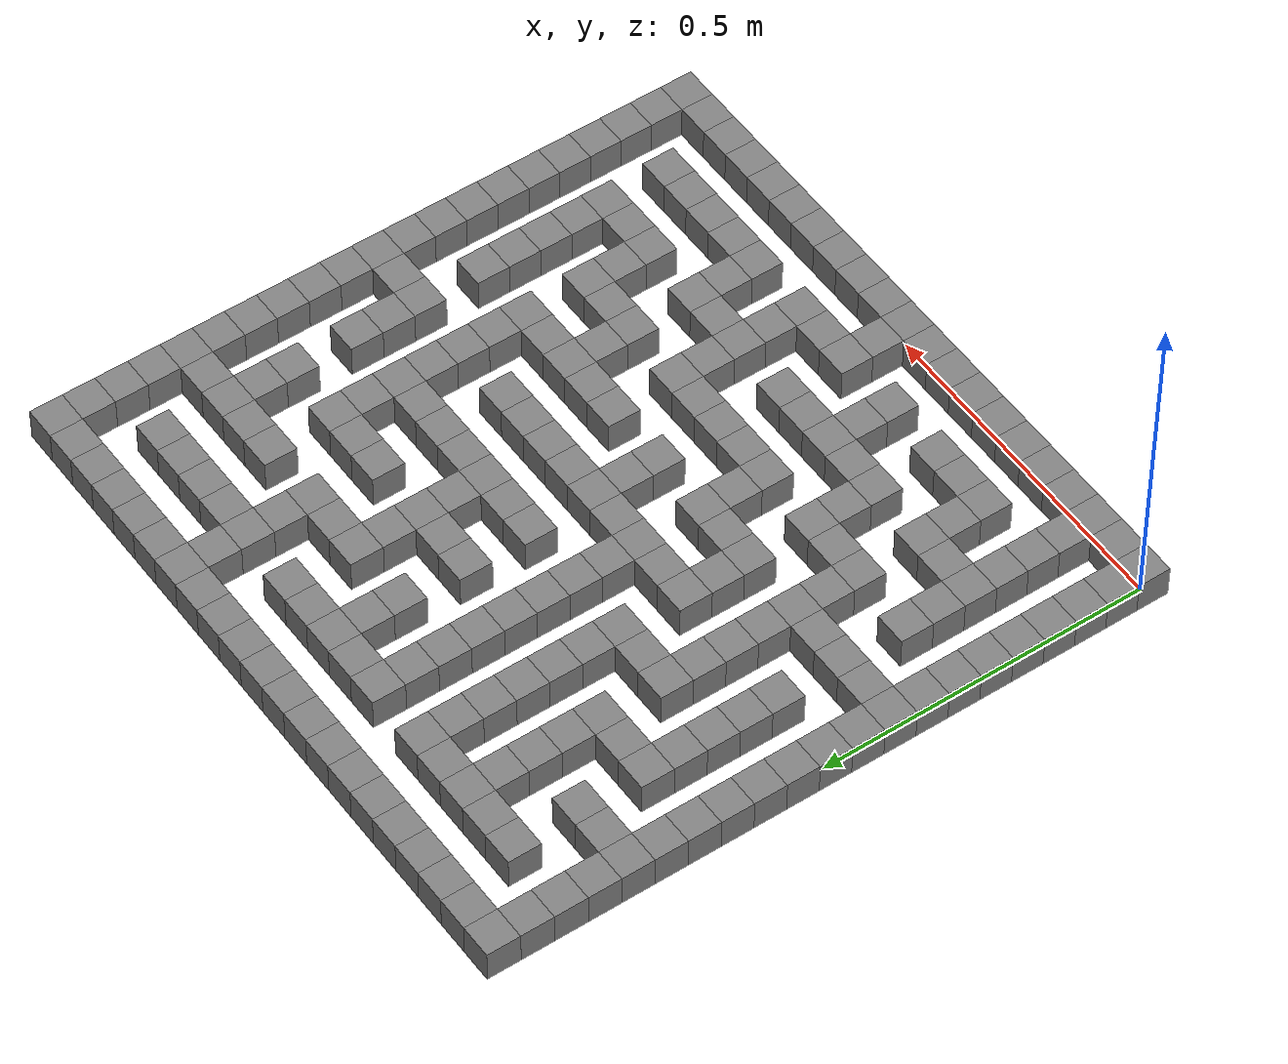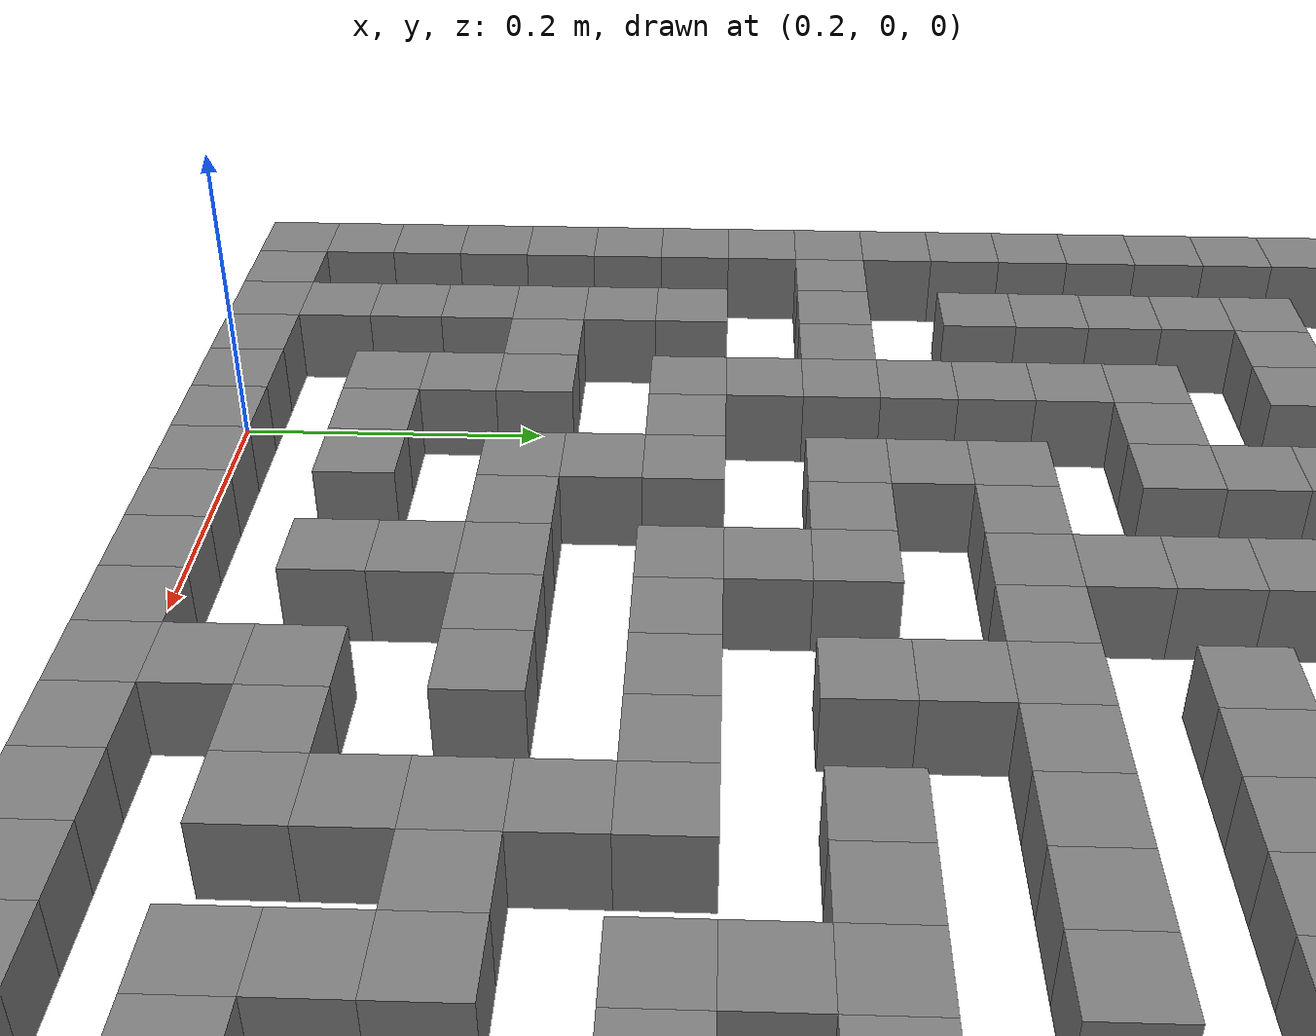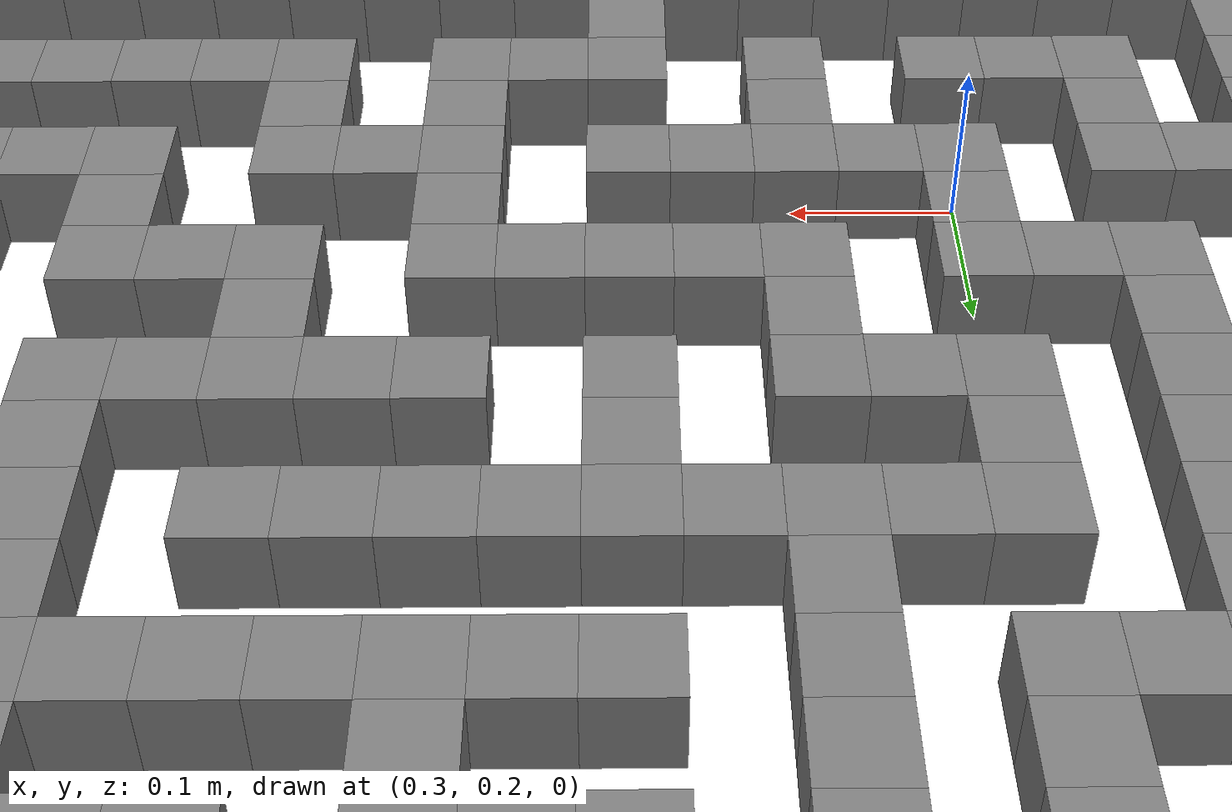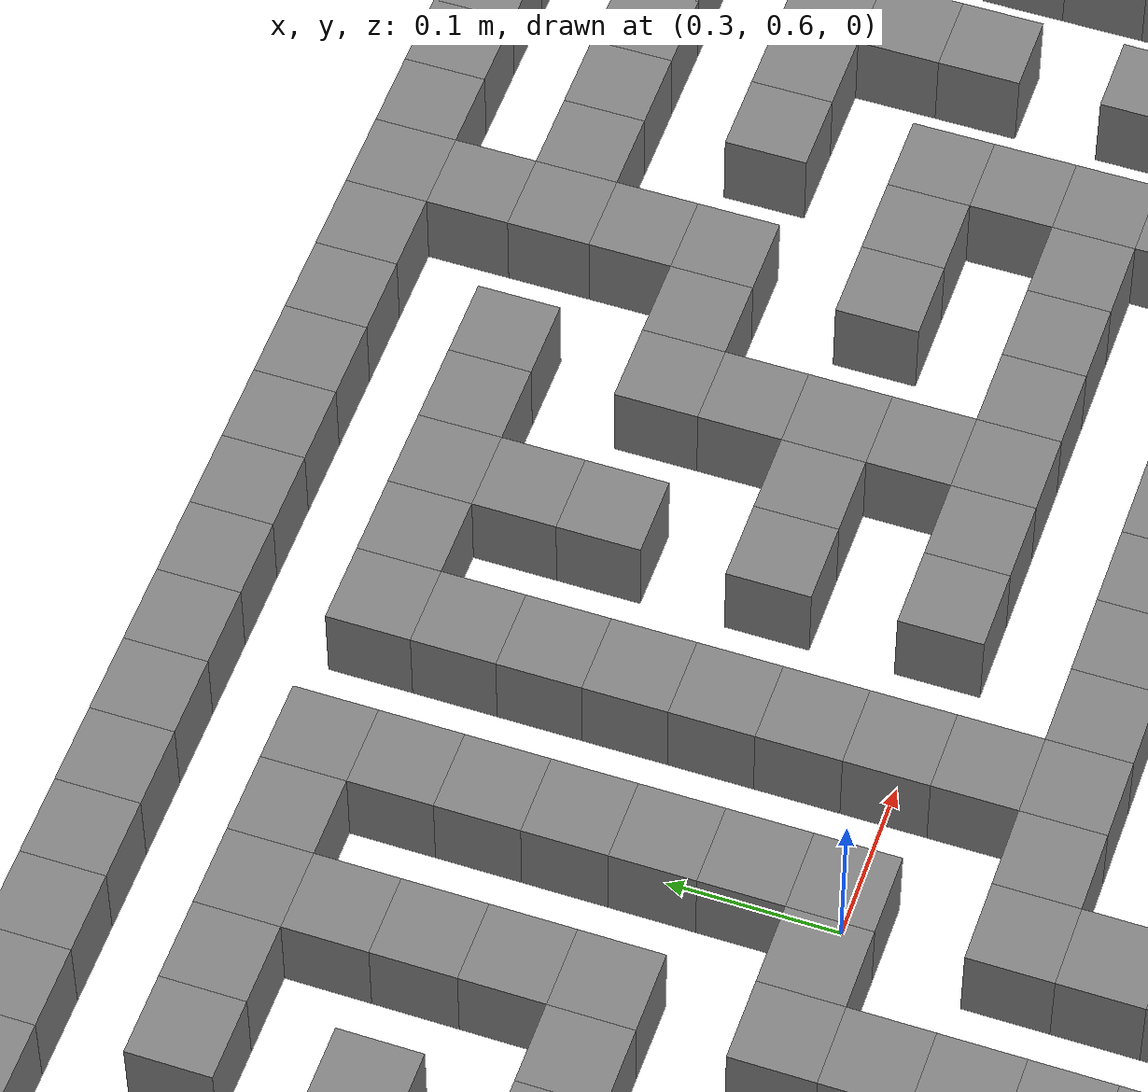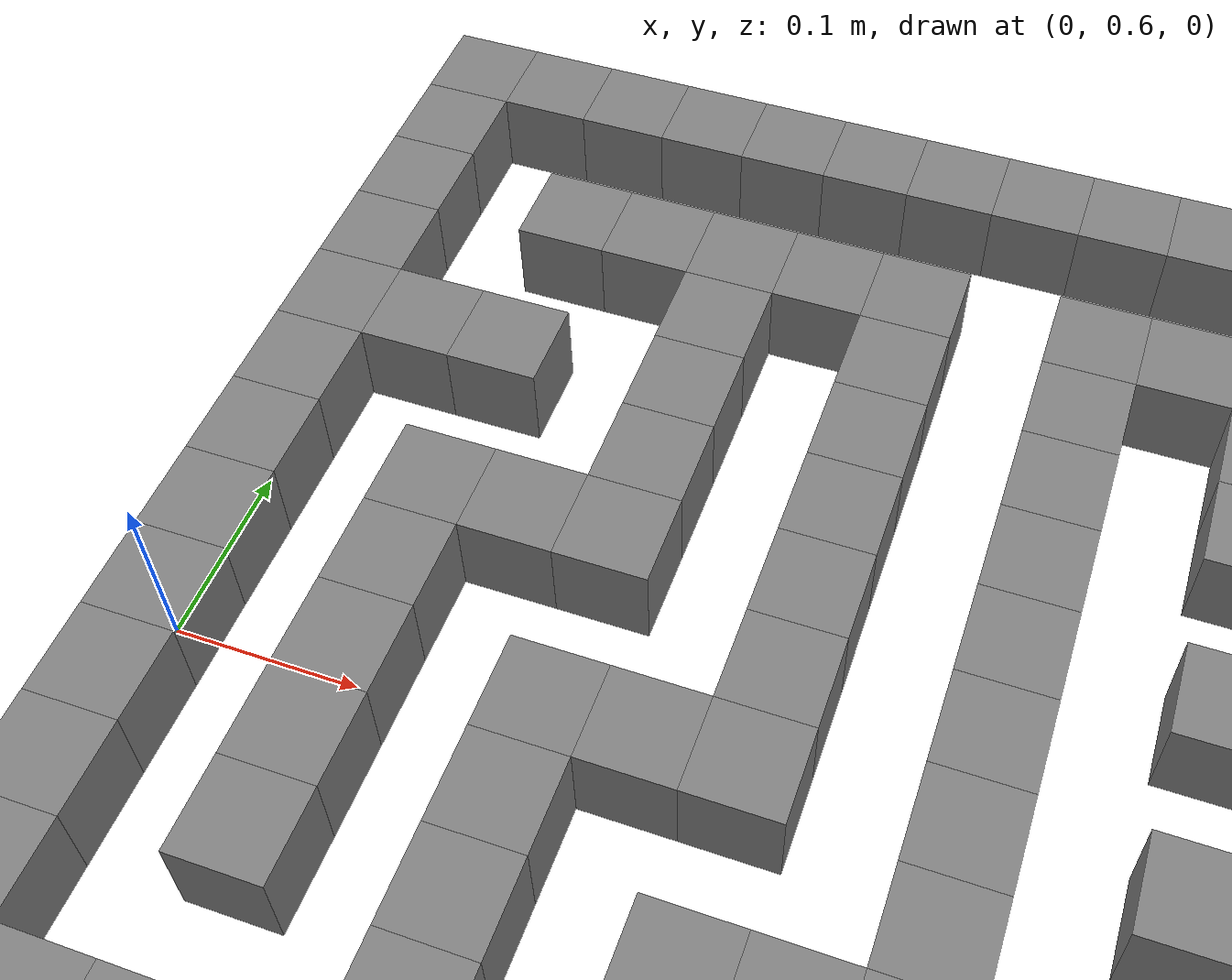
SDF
<?xml version="1.0" ?>
<sdf version="1.9">
  <world name="default">
    <gravity>0 0 -9.81</gravity>
    <light name="sun" type="directional">
      <cast_shadows>true</cast_shadows>
      <pose>0 0 10 0 0 0</pose>
      <diffuse>1 1 1 1</diffuse>
      <specular>0.1 0.1 0.1 1</specular>
      <direction>-0.5 0.5 -1</direction>
    </light>

    <!-- Include the generated model by file path -->
    <include>
      <uri>file:///home/deyung/ros2_newws/src/maze/maze_model.sdf</uri>
      <name>maze</name>
      <pose>0 0 0 0 0 0</pose>
    </include>
  </world>
</sdf>

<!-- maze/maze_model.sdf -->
<sdf version="1.9">
  <model name="maze">
    <static>true</static>

    <link name="wall_0_0">
      <pose>0.0 0.0 0.025 0 0 0</pose>
      <collision name="collision">
        <geometry>
          <box><size>0.05 0.05 0.05</size></box>
        </geometry>
      </collision>
      <visual name="visual">
        <geometry>
          <box><size>0.05 0.05 0.05</size></box>
        </geometry>
        <material><ambient>0.5 0.5 0.5 1</ambient></material>
      </visual>
    </link>

    <link name="wall_0_1">
      <pose>0.0 0.05 0.025 0 0 0</pose>
      <collision name="collision">
        <geometry>
          <box><size>0.05 0.05 0.05</size></box>
        </geometry>
      </collision>
      <visual name="visual">
        <geometry>
          <box><size>0.05 0.05 0.05</size></box>
        </geometry>
        <material><ambient>0.5 0.5 0.5 1</ambient></material>
      </visual>
    </link>

    <link name="wall_0_2">
      <pose>0.0 0.1 0.025 0 0 0</pose>
      <collision name="collision">
        <geometry>
          <box><size>0.05 0.05 0.05</size></box>
        </geometry>
      </collision>
      <visual name="visual">
        <geometry>
          <box><size>0.05 0.05 0.05</size></box>
        </geometry>
        <material><ambient>0.5 0.5 0.5 1</ambient></material>
      </visual>
    </link>

    <link name="wall_0_3">
      <pose>0.0 0.15000000000000002 0.025 0 0 0</pose>
      <collision name="collision">
        <geometry>
          <box><size>0.05 0.05 0.05</size></box>
        </geometry>
      </collision>
      <visual name="visual">
        <geometry>
          <box><size>0.05 0.05 0.05</size></box>
        </geometry>
        <material><ambient>0.5 0.5 0.5 1</ambient></material>
      </visual>
    </link>

    <link name="wall_0_4">
      <pose>0.0 0.2 0.025 0 0 0</pose>
      <collision name="collision">
        <geometry>
          <box><size>0.05 0.05 0.05</size></box>
        </geometry>
      </collision>
      <visual name="visual">
        <geometry>
          <box><size>0.05 0.05 0.05</size></box>
        </geometry>
        <material><ambient>0.5 0.5 0.5 1</ambient></material>
      </visual>
    </link>

    <link name="wall_0_5">
      <pose>0.0 0.25 0.025 0 0 0</pose>
      <collision name="collision">
        <geometry>
          <box><size>0.05 0.05 0.05</size></box>
        </geometry>
      </collision>
      <visual name="visual">
        <geometry>
          <box><size>0.05 0.05 0.05</size></box>
        </geometry>
        <material><ambient>0.5 0.5 0.5 1</ambient></material>
      </visual>
    </link>

    <link name="wall_0_6">
      <pose>0.0 0.30000000000000004 0.025 0 0 0</pose>
      <collision name="collision">
        <geometry>
          <box><size>0.05 0.05 0.05</size></box>
        </geometry>
      </collision>
      <visual name="visual">
        <geometry>
          <box><size>0.05 0.05 0.05</size></box>
        </geometry>
        <material><ambient>0.5 0.5 0.5 1</ambient></material>
      </visual>
    </link>

    <link name="wall_0_7">
      <pose>0.0 0.35000000000000003 0.025 0 0 0</pose>
      <collision name="collision">
        <geometry>
          <box><size>0.05 0.05 0.05</size></box>
        </geometry>
      </collision>
      <visual name="visual">
        <geometry>
          <box><size>0.05 0.05 0.05</size></box>
        </geometry>
        <material><ambient>0.5 0.5 0.5 1</ambient></material>
      </visual>
    </link>

    <link name="wall_0_8">
      <pose>0.0 0.4 0.025 0 0 0</pose>
      <collision name="collision">
        <geometry>
          <box><size>0.05 0.05 0.05</size></box>
        </geometry>
      </collision>
      <visual name="visual">
        <geometry>
          <box><size>0.05 0.05 0.05</size></box>
        </geometry>
        <material><ambient>0.5 0.5 0.5 1</ambient></material>
      </visual>
    </link>

    <link name="wall_0_9">
      <pose>0.0 0.45 0.025 0 0 0</pose>
      <collision name="collision">
        <geometry>
          <box><size>0.05 0.05 0.05</size></box>
        </geometry>
      </collision>
      <visual name="visual">
        <geometry>
          <box><size>0.05 0.05 0.05</size></box>
        </geometry>
        <material><ambient>0.5 0.5 0.5 1</ambient></material>
      </visual>
    </link>

    <link name="wall_0_10">
      <pose>0.0 0.5 0.025 0 0 0</pose>
      <collision name="collision">
        <geometry>
          <box><size>0.05 0.05 0.05</size></box>
        </geometry>
      </collision>
      <visual name="visual">
        <geometry>
          <box><size>0.05 0.05 0.05</size></box>
        </geometry>
        <material><ambient>0.5 0.5 0.5 1</ambient></material>
      </visual>
    </link>

    <link name="wall_0_11">
      <pose>0.0 0.55 0.025 0 0 0</pose>
      <collision name="collision">
        <geometry>
          <box><size>0.05 0.05 0.05</size></box>
        </geometry>
      </collision>
      <visual name="visual">
        <geometry>
          <box><size>0.05 0.05 0.05</size></box>
        </geometry>
        <material><ambient>0.5 0.5 0.5 1</ambient></material>
      </visual>
    </link>

    <link name="wall_0_12">
      <pose>0.0 0.6000000000000001 0.025 0 0 0</pose>
      <collision name="collision">
        <geometry>
          <box><size>0.05 0.05 0.05</size></box>
        </geometry>
      </collision>
      <visual name="visual">
        <geometry>
          <box><size>0.05 0.05 0.05</size></box>
        </geometry>
        <material><ambient>0.5 0.5 0.5 1</ambient></material>
      </visual>
    </link>

    <link name="wall_0_13">
      <pose>0.0 0.65 0.025 0 0 0</pose>
      <collision name="collision">
        <geometry>
          <box><size>0.05 0.05 0.05</size></box>
        </geometry>
      </collision>
      <visual name="visual">
        <geometry>
          <box><size>0.05 0.05 0.05</size></box>
        </geometry>
        <material><ambient>0.5 0.5 0.5 1</ambient></material>
      </visual>
    </link>

    <link name="wall_0_14">
      <pose>0.0 0.7000000000000001 0.025 0 0 0</pose>
      <collision name="collision">
        <geometry>
          <box><size>0.05 0.05 0.05</size></box>
        </geometry>
      </collision>
      <visual name="visual">
        <geometry>
          <box><size>0.05 0.05 0.05</size></box>
        </geometry>
        <material><ambient>0.5 0.5 0.5 1</ambient></material>
      </visual>
    </link>

    <link name="wall_0_15">
      <pose>0.0 0.75 0.025 0 0 0</pose>
      <collision name="collision">
        <geometry>
          <box><size>0.05 0.05 0.05</size></box>
        </geometry>
      </collision>
      <visual name="visual">
        <geometry>
          <box><size>0.05 0.05 0.05</size></box>
        </geometry>
        <material><ambient>0.5 0.5 0.5 1</ambient></material>
      </visual>
    </link>

    <link name="wall_0_16">
      <pose>0.0 0.8 0.025 0 0 0</pose>
      <collision name="collision">
        <geometry>
          <box><size>0.05 0.05 0.05</size></box>
        </geometry>
      </collision>
      <visual name="visual">
        <geometry>
          <box><size>0.05 0.05 0.05</size></box>
        </geometry>
        <material><ambient>0.5 0.5 0.5 1</ambient></material>
      </visual>
    </link>

    <link name="wall_0_17">
      <pose>0.0 0.8500000000000001 0.025 0 0 0</pose>
      <collision name="collision">
        <geometry>
          <box><size>0.05 0.05 0.05</size></box>
        </geometry>
      </collision>
      <visual name="visual">
        <geometry>
          <box><size>0.05 0.05 0.05</size></box>
        </geometry>
        <material><ambient>0.5 0.5 0.5 1</ambient></material>
      </visual>
    </link>

    <link name="wall_0_18">
      <pose>0.0 0.9 0.025 0 0 0</pose>
      <collision name="collision">
        <geometry>
          <box><size>0.05 0.05 0.05</size></box>
        </geometry>
      </collision>
      <visual name="visual">
        <geometry>
          <box><size>0.05 0.05 0.05</size></box>
        </geometry>
        <material><ambient>0.5 0.5 0.5 1</ambient></material>
      </visual>
    </link>

    <link name="wall_0_19">
      <pose>0.0 0.9500000000000001 0.025 0 0 0</pose>
      <collision name="collision">
        <geometry>
          <box><size>0.05 0.05 0.05</size></box>
        </geometry>
      </collision>
      <visual name="visual">
        <geometry>
          <box><size>0.05 0.05 0.05</size></box>
        </geometry>
        <material><ambient>0.5 0.5 0.5 1</ambient></material>
      </visual>
    </link>

    <link name="wall_0_20">
      <pose>0.0 1.0 0.025 0 0 0</pose>
      <collision name="collision">
        <geometry>
          <box><size>0.05 0.05 0.05</size></box>
        </geometry>
      </collision>
      <visual name="visual">
        <geometry>
          <box><size>0.05 0.05 0.05</size></box>
        </geometry>
        <material><ambient>0.5 0.5 0.5 1</ambient></material>
      </visual>
    </link>

    <link name="wall_1_0">
      <pose>0.05 0.0 0.025 0 0 0</pose>
      <collision name="collision">
        <geometry>
          <box><size>0.05 0.05 0.05</size></box>
        </geometry>
      </collision>
      <visual name="visual">
        <geometry>
          <box><size>0.05 0.05 0.05</size></box>
        </geometry>
        <material><ambient>0.5 0.5 0.5 1</ambient></material>
      </visual>
    </link>

    <link name="wall_1_8">
      <pose>0.05 0.4 0.025 0 0 0</pose>
      <collision name="collision">
        <geometry>
          <box><size>0.05 0.05 0.05</size></box>
        </geometry>
      </collision>
      <visual name="visual">
        <geometry>
          <box><size>0.05 0.05 0.05</size></box>
        </geometry>
        <material><ambient>0.5 0.5 0.5 1</ambient></material>
      </visual>
    </link>

    <link name="wall_1_16">
      <pose>0.05 0.8 0.025 0 0 0</pose>
      <collision name="collision">
        <geometry>
          <box><size>0.05 0.05 0.05</size></box>
        </geometry>
      </collision>
      <visual name="visual">
        <geometry>
          <box><size>0.05 0.05 0.05</size></box>
        </geometry>
        <material><ambient>0.5 0.5 0.5 1</ambient></material>
      </visual>
    </link>

    <link name="wall_1_20">
      <pose>0.05 1.0 0.025 0 0 0</pose>
      <collision name="collision">
        <geometry>
          <box><size>0.05 0.05 0.05</size></box>
        </geometry>
      </collision>
      <visual name="visual">
        <geometry>
          <box><size>0.05 0.05 0.05</size></box>
        </geometry>
        <material><ambient>0.5 0.5 0.5 1</ambient></material>
      </visual>
    </link>

    <link name="wall_2_0">
      <pose>0.1 0.0 0.025 0 0 0</pose>
      <collision name="collision">
        <geometry>
          <box><size>0.05 0.05 0.05</size></box>
        </geometry>
      </collision>
      <visual name="visual">
        <geometry>
          <box><size>0.05 0.05 0.05</size></box>
        </geometry>
        <material><ambient>0.5 0.5 0.5 1</ambient></material>
      </visual>
    </link>

    <link name="wall_2_1">
      <pose>0.1 0.05 0.025 0 0 0</pose>
      <collision name="collision">
        <geometry>
          <box><size>0.05 0.05 0.05</size></box>
        </geometry>
      </collision>
      <visual name="visual">
        <geometry>
          <box><size>0.05 0.05 0.05</size></box>
        </geometry>
        <material><ambient>0.5 0.5 0.5 1</ambient></material>
      </visual>
    </link>

    <link name="wall_2_2">
      <pose>0.1 0.1 0.025 0 0 0</pose>
      <collision name="collision">
        <geometry>
          <box><size>0.05 0.05 0.05</size></box>
        </geometry>
      </collision>
      <visual name="visual">
        <geometry>
          <box><size>0.05 0.05 0.05</size></box>
        </geometry>
        <material><ambient>0.5 0.5 0.5 1</ambient></material>
      </visual>
    </link>

    <link name="wall_2_3">
      <pose>0.1 0.15000000000000002 0.025 0 0 0</pose>
      <collision name="collision">
        <geometry>
          <box><size>0.05 0.05 0.05</size></box>
        </geometry>
      </collision>
      <visual name="visual">
        <geometry>
          <box><size>0.05 0.05 0.05</size></box>
        </geometry>
        <material><ambient>0.5 0.5 0.5 1</ambient></material>
      </visual>
    </link>

    <link name="wall_2_4">
      <pose>0.1 0.2 0.025 0 0 0</pose>
      <collision name="collision">
        <geometry>
          <box><size>0.05 0.05 0.05</size></box>
        </geometry>
      </collision>
      <visual name="visual">
        <geometry>
          <box><size>0.05 0.05 0.05</size></box>
        </geometry>
        <material><ambient>0.5 0.5 0.5 1</ambient></material>
      </visual>
    </link>

    <link name="wall_2_5">
      <pose>0.1 0.25 0.025 0 0 0</pose>
      <collision name="collision">
        <geometry>
          <box><size>0.05 0.05 0.05</size></box>
        </geometry>
      </collision>
      <visual name="visual">
        <geometry>
          <box><size>0.05 0.05 0.05</size></box>
        </geometry>
        <material><ambient>0.5 0.5 0.5 1</ambient></material>
      </visual>
    </link>

    <link name="wall_2_6">
      <pose>0.1 0.30000000000000004 0.025 0 0 0</pose>
      <collision name="collision">
        <geometry>
          <box><size>0.05 0.05 0.05</size></box>
        </geometry>
      </collision>
      <visual name="visual">
        <geometry>
          <box><size>0.05 0.05 0.05</size></box>
        </geometry>
        <material><ambient>0.5 0.5 0.5 1</ambient></material>
      </visual>
    </link>

    <link name="wall_2_8">
      <pose>0.1 0.4 0.025 0 0 0</pose>
      <collision name="collision">
        <geometry>
          <box><size>0.05 0.05 0.05</size></box>
        </geometry>
      </collision>
      <visual name="visual">
        <geometry>
          <box><size>0.05 0.05 0.05</size></box>
        </geometry>
        <material><ambient>0.5 0.5 0.5 1</ambient></material>
      </visual>
    </link>

    <link name="wall_2_10">
      <pose>0.1 0.5 0.025 0 0 0</pose>
      <collision name="collision">
        <geometry>
          <box><size>0.05 0.05 0.05</size></box>
        </geometry>
      </collision>
      <visual name="visual">
        <geometry>
          <box><size>0.05 0.05 0.05</size></box>
        </geometry>
        <material><ambient>0.5 0.5 0.5 1</ambient></material>
      </visual>
    </link>

    <link name="wall_2_11">
      <pose>0.1 0.55 0.025 0 0 0</pose>
      <collision name="collision">
        <geometry>
          <box><size>0.05 0.05 0.05</size></box>
        </geometry>
      </collision>
      <visual name="visual">
        <geometry>
          <box><size>0.05 0.05 0.05</size></box>
        </geometry>
        <material><ambient>0.5 0.5 0.5 1</ambient></material>
      </visual>
    </link>

    <link name="wall_2_12">
      <pose>0.1 0.6000000000000001 0.025 0 0 0</pose>
      <collision name="collision">
        <geometry>
          <box><size>0.05 0.05 0.05</size></box>
        </geometry>
      </collision>
      <visual name="visual">
        <geometry>
          <box><size>0.05 0.05 0.05</size></box>
        </geometry>
        <material><ambient>0.5 0.5 0.5 1</ambient></material>
      </visual>
    </link>

    <link name="wall_2_13">
      <pose>0.1 0.65 0.025 0 0 0</pose>
      <collision name="collision">
        <geometry>
          <box><size>0.05 0.05 0.05</size></box>
        </geometry>
      </collision>
      <visual name="visual">
        <geometry>
          <box><size>0.05 0.05 0.05</size></box>
        </geometry>
        <material><ambient>0.5 0.5 0.5 1</ambient></material>
      </visual>
    </link>

    <link name="wall_2_14">
      <pose>0.1 0.7000000000000001 0.025 0 0 0</pose>
      <collision name="collision">
        <geometry>
          <box><size>0.05 0.05 0.05</size></box>
        </geometry>
      </collision>
      <visual name="visual">
        <geometry>
          <box><size>0.05 0.05 0.05</size></box>
        </geometry>
        <material><ambient>0.5 0.5 0.5 1</ambient></material>
      </visual>
    </link>

    <link name="wall_2_16">
      <pose>0.1 0.8 0.025 0 0 0</pose>
      <collision name="collision">
        <geometry>
          <box><size>0.05 0.05 0.05</size></box>
        </geometry>
      </collision>
      <visual name="visual">
        <geometry>
          <box><size>0.05 0.05 0.05</size></box>
        </geometry>
        <material><ambient>0.5 0.5 0.5 1</ambient></material>
      </visual>
    </link>

    <link name="wall_2_18">
      <pose>0.1 0.9 0.025 0 0 0</pose>
      <collision name="collision">
        <geometry>
          <box><size>0.05 0.05 0.05</size></box>
        </geometry>
      </collision>
      <visual name="visual">
        <geometry>
          <box><size>0.05 0.05 0.05</size></box>
        </geometry>
        <material><ambient>0.5 0.5 0.5 1</ambient></material>
      </visual>
    </link>

    <link name="wall_2_20">
      <pose>0.1 1.0 0.025 0 0 0</pose>
      <collision name="collision">
        <geometry>
          <box><size>0.05 0.05 0.05</size></box>
        </geometry>
      </collision>
      <visual name="visual">
        <geometry>
          <box><size>0.05 0.05 0.05</size></box>
        </geometry>
        <material><ambient>0.5 0.5 0.5 1</ambient></material>
      </visual>
    </link>

    <link name="wall_3_0">
      <pose>0.15000000000000002 0.0 0.025 0 0 0</pose>
      <collision name="collision">
        <geometry>
          <box><size>0.05 0.05 0.05</size></box>
        </geometry>
      </collision>
      <visual name="visual">
        <geometry>
          <box><size>0.05 0.05 0.05</size></box>
        </geometry>
        <material><ambient>0.5 0.5 0.5 1</ambient></material>
      </visual>
    </link>

    <link name="wall_3_4">
      <pose>0.15000000000000002 0.2 0.025 0 0 0</pose>
      <collision name="collision">
        <geometry>
          <box><size>0.05 0.05 0.05</size></box>
        </geometry>
      </collision>
      <visual name="visual">
        <geometry>
          <box><size>0.05 0.05 0.05</size></box>
        </geometry>
        <material><ambient>0.5 0.5 0.5 1</ambient></material>
      </visual>
    </link>

    <link name="wall_3_8">
      <pose>0.15000000000000002 0.4 0.025 0 0 0</pose>
      <collision name="collision">
        <geometry>
          <box><size>0.05 0.05 0.05</size></box>
        </geometry>
      </collision>
      <visual name="visual">
        <geometry>
          <box><size>0.05 0.05 0.05</size></box>
        </geometry>
        <material><ambient>0.5 0.5 0.5 1</ambient></material>
      </visual>
    </link>

    <link name="wall_3_14">
      <pose>0.15000000000000002 0.7000000000000001 0.025 0 0 0</pose>
      <collision name="collision">
        <geometry>
          <box><size>0.05 0.05 0.05</size></box>
        </geometry>
      </collision>
      <visual name="visual">
        <geometry>
          <box><size>0.05 0.05 0.05</size></box>
        </geometry>
        <material><ambient>0.5 0.5 0.5 1</ambient></material>
      </visual>
    </link>

    <link name="wall_3_18">
      <pose>0.15000000000000002 0.9 0.025 0 0 0</pose>
      <collision name="collision">
        <geometry>
          <box><size>0.05 0.05 0.05</size></box>
        </geometry>
      </collision>
      <visual name="visual">
        <geometry>
          <box><size>0.05 0.05 0.05</size></box>
        </geometry>
        <material><ambient>0.5 0.5 0.5 1</ambient></material>
      </visual>
    </link>

    <link name="wall_3_20">
      <pose>0.15000000000000002 1.0 0.025 0 0 0</pose>
      <collision name="collision">
        <geometry>
          <box><size>0.05 0.05 0.05</size></box>
        </geometry>
      </collision>
      <visual name="visual">
        <geometry>
          <box><size>0.05 0.05 0.05</size></box>
        </geometry>
        <material><ambient>0.5 0.5 0.5 1</ambient></material>
      </visual>
    </link>

    <link name="wall_4_0">
      <pose>0.2 0.0 0.025 0 0 0</pose>
      <collision name="collision">
        <geometry>
          <box><size>0.05 0.05 0.05</size></box>
        </geometry>
      </collision>
      <visual name="visual">
        <geometry>
          <box><size>0.05 0.05 0.05</size></box>
        </geometry>
        <material><ambient>0.5 0.5 0.5 1</ambient></material>
      </visual>
    </link>

    <link name="wall_4_2">
      <pose>0.2 0.1 0.025 0 0 0</pose>
      <collision name="collision">
        <geometry>
          <box><size>0.05 0.05 0.05</size></box>
        </geometry>
      </collision>
      <visual name="visual">
        <geometry>
          <box><size>0.05 0.05 0.05</size></box>
        </geometry>
        <material><ambient>0.5 0.5 0.5 1</ambient></material>
      </visual>
    </link>

    <link name="wall_4_3">
      <pose>0.2 0.15000000000000002 0.025 0 0 0</pose>
      <collision name="collision">
        <geometry>
          <box><size>0.05 0.05 0.05</size></box>
        </geometry>
      </collision>
      <visual name="visual">
        <geometry>
          <box><size>0.05 0.05 0.05</size></box>
        </geometry>
        <material><ambient>0.5 0.5 0.5 1</ambient></material>
      </visual>
    </link>

    <link name="wall_4_4">
      <pose>0.2 0.2 0.025 0 0 0</pose>
      <collision name="collision">
        <geometry>
          <box><size>0.05 0.05 0.05</size></box>
        </geometry>
      </collision>
      <visual name="visual">
        <geometry>
          <box><size>0.05 0.05 0.05</size></box>
        </geometry>
        <material><ambient>0.5 0.5 0.5 1</ambient></material>
      </visual>
    </link>

    <link name="wall_4_6">
      <pose>0.2 0.30000000000000004 0.025 0 0 0</pose>
      <collision name="collision">
        <geometry>
          <box><size>0.05 0.05 0.05</size></box>
        </geometry>
      </collision>
      <visual name="visual">
        <geometry>
          <box><size>0.05 0.05 0.05</size></box>
        </geometry>
        <material><ambient>0.5 0.5 0.5 1</ambient></material>
      </visual>
    </link>

    <link name="wall_4_7">
      <pose>0.2 0.35000000000000003 0.025 0 0 0</pose>
      <collision name="collision">
        <geometry>
          <box><size>0.05 0.05 0.05</size></box>
        </geometry>
      </collision>
      <visual name="visual">
        <geometry>
          <box><size>0.05 0.05 0.05</size></box>
        </geometry>
        <material><ambient>0.5 0.5 0.5 1</ambient></material>
      </visual>
    </link>

    <link name="wall_4_8">
      <pose>0.2 0.4 0.025 0 0 0</pose>
      <collision name="collision">
        <geometry>
          <box><size>0.05 0.05 0.05</size></box>
        </geometry>
      </collision>
      <visual name="visual">
        <geometry>
          <box><size>0.05 0.05 0.05</size></box>
        </geometry>
        <material><ambient>0.5 0.5 0.5 1</ambient></material>
      </visual>
    </link>

    <link name="wall_4_9">
      <pose>0.2 0.45 0.025 0 0 0</pose>
      <collision name="collision">
        <geometry>
          <box><size>0.05 0.05 0.05</size></box>
        </geometry>
      </collision>
      <visual name="visual">
        <geometry>
          <box><size>0.05 0.05 0.05</size></box>
        </geometry>
        <material><ambient>0.5 0.5 0.5 1</ambient></material>
      </visual>
    </link>

    <link name="wall_4_10">
      <pose>0.2 0.5 0.025 0 0 0</pose>
      <collision name="collision">
        <geometry>
          <box><size>0.05 0.05 0.05</size></box>
        </geometry>
      </collision>
      <visual name="visual">
        <geometry>
          <box><size>0.05 0.05 0.05</size></box>
        </geometry>
        <material><ambient>0.5 0.5 0.5 1</ambient></material>
      </visual>
    </link>

    <link name="wall_4_11">
      <pose>0.2 0.55 0.025 0 0 0</pose>
      <collision name="collision">
        <geometry>
          <box><size>0.05 0.05 0.05</size></box>
        </geometry>
      </collision>
      <visual name="visual">
        <geometry>
          <box><size>0.05 0.05 0.05</size></box>
        </geometry>
        <material><ambient>0.5 0.5 0.5 1</ambient></material>
      </visual>
    </link>

    <link name="wall_4_12">
      <pose>0.2 0.6000000000000001 0.025 0 0 0</pose>
      <collision name="collision">
        <geometry>
          <box><size>0.05 0.05 0.05</size></box>
        </geometry>
      </collision>
      <visual name="visual">
        <geometry>
          <box><size>0.05 0.05 0.05</size></box>
        </geometry>
        <material><ambient>0.5 0.5 0.5 1</ambient></material>
      </visual>
    </link>

    <link name="wall_4_14">
      <pose>0.2 0.7000000000000001 0.025 0 0 0</pose>
      <collision name="collision">
        <geometry>
          <box><size>0.05 0.05 0.05</size></box>
        </geometry>
      </collision>
      <visual name="visual">
        <geometry>
          <box><size>0.05 0.05 0.05</size></box>
        </geometry>
        <material><ambient>0.5 0.5 0.5 1</ambient></material>
      </visual>
    </link>

    <link name="wall_4_15">
      <pose>0.2 0.75 0.025 0 0 0</pose>
      <collision name="collision">
        <geometry>
          <box><size>0.05 0.05 0.05</size></box>
        </geometry>
      </collision>
      <visual name="visual">
        <geometry>
          <box><size>0.05 0.05 0.05</size></box>
        </geometry>
        <material><ambient>0.5 0.5 0.5 1</ambient></material>
      </visual>
    </link>

    <link name="wall_4_16">
      <pose>0.2 0.8 0.025 0 0 0</pose>
      <collision name="collision">
        <geometry>
          <box><size>0.05 0.05 0.05</size></box>
        </geometry>
      </collision>
      <visual name="visual">
        <geometry>
          <box><size>0.05 0.05 0.05</size></box>
        </geometry>
        <material><ambient>0.5 0.5 0.5 1</ambient></material>
      </visual>
    </link>

    <link name="wall_4_17">
      <pose>0.2 0.8500000000000001 0.025 0 0 0</pose>
      <collision name="collision">
        <geometry>
          <box><size>0.05 0.05 0.05</size></box>
        </geometry>
      </collision>
      <visual name="visual">
        <geometry>
          <box><size>0.05 0.05 0.05</size></box>
        </geometry>
        <material><ambient>0.5 0.5 0.5 1</ambient></material>
      </visual>
    </link>

    <link name="wall_4_18">
      <pose>0.2 0.9 0.025 0 0 0</pose>
      <collision name="collision">
        <geometry>
          <box><size>0.05 0.05 0.05</size></box>
        </geometry>
      </collision>
      <visual name="visual">
        <geometry>
          <box><size>0.05 0.05 0.05</size></box>
        </geometry>
        <material><ambient>0.5 0.5 0.5 1</ambient></material>
      </visual>
    </link>

    <link name="wall_4_20">
      <pose>0.2 1.0 0.025 0 0 0</pose>
      <collision name="collision">
        <geometry>
          <box><size>0.05 0.05 0.05</size></box>
        </geometry>
      </collision>
      <visual name="visual">
        <geometry>
          <box><size>0.05 0.05 0.05</size></box>
        </geometry>
        <material><ambient>0.5 0.5 0.5 1</ambient></material>
      </visual>
    </link>

    <link name="wall_5_0">
      <pose>0.25 0.0 0.025 0 0 0</pose>
      <collision name="collision">
        <geometry>
          <box><size>0.05 0.05 0.05</size></box>
        </geometry>
      </collision>
      <visual name="visual">
        <geometry>
          <box><size>0.05 0.05 0.05</size></box>
        </geometry>
        <material><ambient>0.5 0.5 0.5 1</ambient></material>
      </visual>
    </link>

    <link name="wall_5_2">
      <pose>0.25 0.1 0.025 0 0 0</pose>
      <collision name="collision">
        <geometry>
          <box><size>0.05 0.05 0.05</size></box>
        </geometry>
      </collision>
      <visual name="visual">
        <geometry>
          <box><size>0.05 0.05 0.05</size></box>
        </geometry>
        <material><ambient>0.5 0.5 0.5 1</ambient></material>
      </visual>
    </link>

    <link name="wall_5_6">
      <pose>0.25 0.30000000000000004 0.025 0 0 0</pose>
      <collision name="collision">
        <geometry>
          <box><size>0.05 0.05 0.05</size></box>
        </geometry>
      </collision>
      <visual name="visual">
        <geometry>
          <box><size>0.05 0.05 0.05</size></box>
        </geometry>
        <material><ambient>0.5 0.5 0.5 1</ambient></material>
      </visual>
    </link>

    <link name="wall_5_12">
      <pose>0.25 0.6000000000000001 0.025 0 0 0</pose>
      <collision name="collision">
        <geometry>
          <box><size>0.05 0.05 0.05</size></box>
        </geometry>
      </collision>
      <visual name="visual">
        <geometry>
          <box><size>0.05 0.05 0.05</size></box>
        </geometry>
        <material><ambient>0.5 0.5 0.5 1</ambient></material>
      </visual>
    </link>

    <link name="wall_5_18">
      <pose>0.25 0.9 0.025 0 0 0</pose>
      <collision name="collision">
        <geometry>
          <box><size>0.05 0.05 0.05</size></box>
        </geometry>
      </collision>
      <visual name="visual">
        <geometry>
          <box><size>0.05 0.05 0.05</size></box>
        </geometry>
        <material><ambient>0.5 0.5 0.5 1</ambient></material>
      </visual>
    </link>

    <link name="wall_5_20">
      <pose>0.25 1.0 0.025 0 0 0</pose>
      <collision name="collision">
        <geometry>
          <box><size>0.05 0.05 0.05</size></box>
        </geometry>
      </collision>
      <visual name="visual">
        <geometry>
          <box><size>0.05 0.05 0.05</size></box>
        </geometry>
        <material><ambient>0.5 0.5 0.5 1</ambient></material>
      </visual>
    </link>

    <link name="wall_6_0">
      <pose>0.30000000000000004 0.0 0.025 0 0 0</pose>
      <collision name="collision">
        <geometry>
          <box><size>0.05 0.05 0.05</size></box>
        </geometry>
      </collision>
      <visual name="visual">
        <geometry>
          <box><size>0.05 0.05 0.05</size></box>
        </geometry>
        <material><ambient>0.5 0.5 0.5 1</ambient></material>
      </visual>
    </link>

    <link name="wall_6_2">
      <pose>0.30000000000000004 0.1 0.025 0 0 0</pose>
      <collision name="collision">
        <geometry>
          <box><size>0.05 0.05 0.05</size></box>
        </geometry>
      </collision>
      <visual name="visual">
        <geometry>
          <box><size>0.05 0.05 0.05</size></box>
        </geometry>
        <material><ambient>0.5 0.5 0.5 1</ambient></material>
      </visual>
    </link>

    <link name="wall_6_4">
      <pose>0.30000000000000004 0.2 0.025 0 0 0</pose>
      <collision name="collision">
        <geometry>
          <box><size>0.05 0.05 0.05</size></box>
        </geometry>
      </collision>
      <visual name="visual">
        <geometry>
          <box><size>0.05 0.05 0.05</size></box>
        </geometry>
        <material><ambient>0.5 0.5 0.5 1</ambient></material>
      </visual>
    </link>

    <link name="wall_6_5">
      <pose>0.30000000000000004 0.25 0.025 0 0 0</pose>
      <collision name="collision">
        <geometry>
          <box><size>0.05 0.05 0.05</size></box>
        </geometry>
      </collision>
      <visual name="visual">
        <geometry>
          <box><size>0.05 0.05 0.05</size></box>
        </geometry>
        <material><ambient>0.5 0.5 0.5 1</ambient></material>
      </visual>
    </link>

    <link name="wall_6_6">
      <pose>0.30000000000000004 0.30000000000000004 0.025 0 0 0</pose>
      <collision name="collision">
        <geometry>
          <box><size>0.05 0.05 0.05</size></box>
        </geometry>
      </collision>
      <visual name="visual">
        <geometry>
          <box><size>0.05 0.05 0.05</size></box>
        </geometry>
        <material><ambient>0.5 0.5 0.5 1</ambient></material>
      </visual>
    </link>

    <link name="wall_6_8">
      <pose>0.30000000000000004 0.4 0.025 0 0 0</pose>
      <collision name="collision">
        <geometry>
          <box><size>0.05 0.05 0.05</size></box>
        </geometry>
      </collision>
      <visual name="visual">
        <geometry>
          <box><size>0.05 0.05 0.05</size></box>
        </geometry>
        <material><ambient>0.5 0.5 0.5 1</ambient></material>
      </visual>
    </link>

    <link name="wall_6_9">
      <pose>0.30000000000000004 0.45 0.025 0 0 0</pose>
      <collision name="collision">
        <geometry>
          <box><size>0.05 0.05 0.05</size></box>
        </geometry>
      </collision>
      <visual name="visual">
        <geometry>
          <box><size>0.05 0.05 0.05</size></box>
        </geometry>
        <material><ambient>0.5 0.5 0.5 1</ambient></material>
      </visual>
    </link>

    <link name="wall_6_10">
      <pose>0.30000000000000004 0.5 0.025 0 0 0</pose>
      <collision name="collision">
        <geometry>
          <box><size>0.05 0.05 0.05</size></box>
        </geometry>
      </collision>
      <visual name="visual">
        <geometry>
          <box><size>0.05 0.05 0.05</size></box>
        </geometry>
        <material><ambient>0.5 0.5 0.5 1</ambient></material>
      </visual>
    </link>

    <link name="wall_6_12">
      <pose>0.30000000000000004 0.6000000000000001 0.025 0 0 0</pose>
      <collision name="collision">
        <geometry>
          <box><size>0.05 0.05 0.05</size></box>
        </geometry>
      </collision>
      <visual name="visual">
        <geometry>
          <box><size>0.05 0.05 0.05</size></box>
        </geometry>
        <material><ambient>0.5 0.5 0.5 1</ambient></material>
      </visual>
    </link>

    <link name="wall_6_13">
      <pose>0.30000000000000004 0.65 0.025 0 0 0</pose>
      <collision name="collision">
        <geometry>
          <box><size>0.05 0.05 0.05</size></box>
        </geometry>
      </collision>
      <visual name="visual">
        <geometry>
          <box><size>0.05 0.05 0.05</size></box>
        </geometry>
        <material><ambient>0.5 0.5 0.5 1</ambient></material>
      </visual>
    </link>

    <link name="wall_6_14">
      <pose>0.30000000000000004 0.7000000000000001 0.025 0 0 0</pose>
      <collision name="collision">
        <geometry>
          <box><size>0.05 0.05 0.05</size></box>
        </geometry>
      </collision>
      <visual name="visual">
        <geometry>
          <box><size>0.05 0.05 0.05</size></box>
        </geometry>
        <material><ambient>0.5 0.5 0.5 1</ambient></material>
      </visual>
    </link>

    <link name="wall_6_15">
      <pose>0.30000000000000004 0.75 0.025 0 0 0</pose>
      <collision name="collision">
        <geometry>
          <box><size>0.05 0.05 0.05</size></box>
        </geometry>
      </collision>
      <visual name="visual">
        <geometry>
          <box><size>0.05 0.05 0.05</size></box>
        </geometry>
        <material><ambient>0.5 0.5 0.5 1</ambient></material>
      </visual>
    </link>

    <link name="wall_6_16">
      <pose>0.30000000000000004 0.8 0.025 0 0 0</pose>
      <collision name="collision">
        <geometry>
          <box><size>0.05 0.05 0.05</size></box>
        </geometry>
      </collision>
      <visual name="visual">
        <geometry>
          <box><size>0.05 0.05 0.05</size></box>
        </geometry>
        <material><ambient>0.5 0.5 0.5 1</ambient></material>
      </visual>
    </link>

    <link name="wall_6_17">
      <pose>0.30000000000000004 0.8500000000000001 0.025 0 0 0</pose>
      <collision name="collision">
        <geometry>
          <box><size>0.05 0.05 0.05</size></box>
        </geometry>
      </collision>
      <visual name="visual">
        <geometry>
          <box><size>0.05 0.05 0.05</size></box>
        </geometry>
        <material><ambient>0.5 0.5 0.5 1</ambient></material>
      </visual>
    </link>

    <link name="wall_6_18">
      <pose>0.30000000000000004 0.9 0.025 0 0 0</pose>
      <collision name="collision">
        <geometry>
          <box><size>0.05 0.05 0.05</size></box>
        </geometry>
      </collision>
      <visual name="visual">
        <geometry>
          <box><size>0.05 0.05 0.05</size></box>
        </geometry>
        <material><ambient>0.5 0.5 0.5 1</ambient></material>
      </visual>
    </link>

    <link name="wall_6_20">
      <pose>0.30000000000000004 1.0 0.025 0 0 0</pose>
      <collision name="collision">
        <geometry>
          <box><size>0.05 0.05 0.05</size></box>
        </geometry>
      </collision>
      <visual name="visual">
        <geometry>
          <box><size>0.05 0.05 0.05</size></box>
        </geometry>
        <material><ambient>0.5 0.5 0.5 1</ambient></material>
      </visual>
    </link>

    <link name="wall_7_0">
      <pose>0.35000000000000003 0.0 0.025 0 0 0</pose>
      <collision name="collision">
        <geometry>
          <box><size>0.05 0.05 0.05</size></box>
        </geometry>
      </collision>
      <visual name="visual">
        <geometry>
          <box><size>0.05 0.05 0.05</size></box>
        </geometry>
        <material><ambient>0.5 0.5 0.5 1</ambient></material>
      </visual>
    </link>

    <link name="wall_7_4">
      <pose>0.35000000000000003 0.2 0.025 0 0 0</pose>
      <collision name="collision">
        <geometry>
          <box><size>0.05 0.05 0.05</size></box>
        </geometry>
      </collision>
      <visual name="visual">
        <geometry>
          <box><size>0.05 0.05 0.05</size></box>
        </geometry>
        <material><ambient>0.5 0.5 0.5 1</ambient></material>
      </visual>
    </link>

    <link name="wall_7_8">
      <pose>0.35000000000000003 0.4 0.025 0 0 0</pose>
      <collision name="collision">
        <geometry>
          <box><size>0.05 0.05 0.05</size></box>
        </geometry>
      </collision>
      <visual name="visual">
        <geometry>
          <box><size>0.05 0.05 0.05</size></box>
        </geometry>
        <material><ambient>0.5 0.5 0.5 1</ambient></material>
      </visual>
    </link>

    <link name="wall_7_10">
      <pose>0.35000000000000003 0.5 0.025 0 0 0</pose>
      <collision name="collision">
        <geometry>
          <box><size>0.05 0.05 0.05</size></box>
        </geometry>
      </collision>
      <visual name="visual">
        <geometry>
          <box><size>0.05 0.05 0.05</size></box>
        </geometry>
        <material><ambient>0.5 0.5 0.5 1</ambient></material>
      </visual>
    </link>

    <link name="wall_7_20">
      <pose>0.35000000000000003 1.0 0.025 0 0 0</pose>
      <collision name="collision">
        <geometry>
          <box><size>0.05 0.05 0.05</size></box>
        </geometry>
      </collision>
      <visual name="visual">
        <geometry>
          <box><size>0.05 0.05 0.05</size></box>
        </geometry>
        <material><ambient>0.5 0.5 0.5 1</ambient></material>
      </visual>
    </link>

    <link name="wall_8_0">
      <pose>0.4 0.0 0.025 0 0 0</pose>
      <collision name="collision">
        <geometry>
          <box><size>0.05 0.05 0.05</size></box>
        </geometry>
      </collision>
      <visual name="visual">
        <geometry>
          <box><size>0.05 0.05 0.05</size></box>
        </geometry>
        <material><ambient>0.5 0.5 0.5 1</ambient></material>
      </visual>
    </link>

    <link name="wall_8_2">
      <pose>0.4 0.1 0.025 0 0 0</pose>
      <collision name="collision">
        <geometry>
          <box><size>0.05 0.05 0.05</size></box>
        </geometry>
      </collision>
      <visual name="visual">
        <geometry>
          <box><size>0.05 0.05 0.05</size></box>
        </geometry>
        <material><ambient>0.5 0.5 0.5 1</ambient></material>
      </visual>
    </link>

    <link name="wall_8_3">
      <pose>0.4 0.15000000000000002 0.025 0 0 0</pose>
      <collision name="collision">
        <geometry>
          <box><size>0.05 0.05 0.05</size></box>
        </geometry>
      </collision>
      <visual name="visual">
        <geometry>
          <box><size>0.05 0.05 0.05</size></box>
        </geometry>
        <material><ambient>0.5 0.5 0.5 1</ambient></material>
      </visual>
    </link>

    <link name="wall_8_4">
      <pose>0.4 0.2 0.025 0 0 0</pose>
      <collision name="collision">
        <geometry>
          <box><size>0.05 0.05 0.05</size></box>
        </geometry>
      </collision>
      <visual name="visual">
        <geometry>
          <box><size>0.05 0.05 0.05</size></box>
        </geometry>
        <material><ambient>0.5 0.5 0.5 1</ambient></material>
      </visual>
    </link>

    <link name="wall_8_6">
      <pose>0.4 0.30000000000000004 0.025 0 0 0</pose>
      <collision name="collision">
        <geometry>
          <box><size>0.05 0.05 0.05</size></box>
        </geometry>
      </collision>
      <visual name="visual">
        <geometry>
          <box><size>0.05 0.05 0.05</size></box>
        </geometry>
        <material><ambient>0.5 0.5 0.5 1</ambient></material>
      </visual>
    </link>

    <link name="wall_8_7">
      <pose>0.4 0.35000000000000003 0.025 0 0 0</pose>
      <collision name="collision">
        <geometry>
          <box><size>0.05 0.05 0.05</size></box>
        </geometry>
      </collision>
      <visual name="visual">
        <geometry>
          <box><size>0.05 0.05 0.05</size></box>
        </geometry>
        <material><ambient>0.5 0.5 0.5 1</ambient></material>
      </visual>
    </link>

    <link name="wall_8_8">
      <pose>0.4 0.4 0.025 0 0 0</pose>
      <collision name="collision">
        <geometry>
          <box><size>0.05 0.05 0.05</size></box>
        </geometry>
      </collision>
      <visual name="visual">
        <geometry>
          <box><size>0.05 0.05 0.05</size></box>
        </geometry>
        <material><ambient>0.5 0.5 0.5 1</ambient></material>
      </visual>
    </link>

    <link name="wall_8_10">
      <pose>0.4 0.5 0.025 0 0 0</pose>
      <collision name="collision">
        <geometry>
          <box><size>0.05 0.05 0.05</size></box>
        </geometry>
      </collision>
      <visual name="visual">
        <geometry>
          <box><size>0.05 0.05 0.05</size></box>
        </geometry>
        <material><ambient>0.5 0.5 0.5 1</ambient></material>
      </visual>
    </link>

    <link name="wall_8_11">
      <pose>0.4 0.55 0.025 0 0 0</pose>
      <collision name="collision">
        <geometry>
          <box><size>0.05 0.05 0.05</size></box>
        </geometry>
      </collision>
      <visual name="visual">
        <geometry>
          <box><size>0.05 0.05 0.05</size></box>
        </geometry>
        <material><ambient>0.5 0.5 0.5 1</ambient></material>
      </visual>
    </link>

    <link name="wall_8_12">
      <pose>0.4 0.6000000000000001 0.025 0 0 0</pose>
      <collision name="collision">
        <geometry>
          <box><size>0.05 0.05 0.05</size></box>
        </geometry>
      </collision>
      <visual name="visual">
        <geometry>
          <box><size>0.05 0.05 0.05</size></box>
        </geometry>
        <material><ambient>0.5 0.5 0.5 1</ambient></material>
      </visual>
    </link>

    <link name="wall_8_13">
      <pose>0.4 0.65 0.025 0 0 0</pose>
      <collision name="collision">
        <geometry>
          <box><size>0.05 0.05 0.05</size></box>
        </geometry>
      </collision>
      <visual name="visual">
        <geometry>
          <box><size>0.05 0.05 0.05</size></box>
        </geometry>
        <material><ambient>0.5 0.5 0.5 1</ambient></material>
      </visual>
    </link>

    <link name="wall_8_14">
      <pose>0.4 0.7000000000000001 0.025 0 0 0</pose>
      <collision name="collision">
        <geometry>
          <box><size>0.05 0.05 0.05</size></box>
        </geometry>
      </collision>
      <visual name="visual">
        <geometry>
          <box><size>0.05 0.05 0.05</size></box>
        </geometry>
        <material><ambient>0.5 0.5 0.5 1</ambient></material>
      </visual>
    </link>

    <link name="wall_8_15">
      <pose>0.4 0.75 0.025 0 0 0</pose>
      <collision name="collision">
        <geometry>
          <box><size>0.05 0.05 0.05</size></box>
        </geometry>
      </collision>
      <visual name="visual">
        <geometry>
          <box><size>0.05 0.05 0.05</size></box>
        </geometry>
        <material><ambient>0.5 0.5 0.5 1</ambient></material>
      </visual>
    </link>

    <link name="wall_8_16">
      <pose>0.4 0.8 0.025 0 0 0</pose>
      <collision name="collision">
        <geometry>
          <box><size>0.05 0.05 0.05</size></box>
        </geometry>
      </collision>
      <visual name="visual">
        <geometry>
          <box><size>0.05 0.05 0.05</size></box>
        </geometry>
        <material><ambient>0.5 0.5 0.5 1</ambient></material>
      </visual>
    </link>

    <link name="wall_8_17">
      <pose>0.4 0.8500000000000001 0.025 0 0 0</pose>
      <collision name="collision">
        <geometry>
          <box><size>0.05 0.05 0.05</size></box>
        </geometry>
      </collision>
      <visual name="visual">
        <geometry>
          <box><size>0.05 0.05 0.05</size></box>
        </geometry>
        <material><ambient>0.5 0.5 0.5 1</ambient></material>
      </visual>
    </link>

    <link name="wall_8_18">
      <pose>0.4 0.9 0.025 0 0 0</pose>
      <collision name="collision">
        <geometry>
          <box><size>0.05 0.05 0.05</size></box>
        </geometry>
      </collision>
      <visual name="visual">
        <geometry>
          <box><size>0.05 0.05 0.05</size></box>
        </geometry>
        <material><ambient>0.5 0.5 0.5 1</ambient></material>
      </visual>
    </link>

    <link name="wall_8_20">
      <pose>0.4 1.0 0.025 0 0 0</pose>
      <collision name="collision">
        <geometry>
          <box><size>0.05 0.05 0.05</size></box>
        </geometry>
      </collision>
      <visual name="visual">
        <geometry>
          <box><size>0.05 0.05 0.05</size></box>
        </geometry>
        <material><ambient>0.5 0.5 0.5 1</ambient></material>
      </visual>
    </link>

    <link name="wall_9_0">
      <pose>0.45 0.0 0.025 0 0 0</pose>
      <collision name="collision">
        <geometry>
          <box><size>0.05 0.05 0.05</size></box>
        </geometry>
      </collision>
      <visual name="visual">
        <geometry>
          <box><size>0.05 0.05 0.05</size></box>
        </geometry>
        <material><ambient>0.5 0.5 0.5 1</ambient></material>
      </visual>
    </link>

    <link name="wall_9_4">
      <pose>0.45 0.2 0.025 0 0 0</pose>
      <collision name="collision">
        <geometry>
          <box><size>0.05 0.05 0.05</size></box>
        </geometry>
      </collision>
      <visual name="visual">
        <geometry>
          <box><size>0.05 0.05 0.05</size></box>
        </geometry>
        <material><ambient>0.5 0.5 0.5 1</ambient></material>
      </visual>
    </link>

    <link name="wall_9_6">
      <pose>0.45 0.30000000000000004 0.025 0 0 0</pose>
      <collision name="collision">
        <geometry>
          <box><size>0.05 0.05 0.05</size></box>
        </geometry>
      </collision>
      <visual name="visual">
        <geometry>
          <box><size>0.05 0.05 0.05</size></box>
        </geometry>
        <material><ambient>0.5 0.5 0.5 1</ambient></material>
      </visual>
    </link>

    <link name="wall_9_10">
      <pose>0.45 0.5 0.025 0 0 0</pose>
      <collision name="collision">
        <geometry>
          <box><size>0.05 0.05 0.05</size></box>
        </geometry>
      </collision>
      <visual name="visual">
        <geometry>
          <box><size>0.05 0.05 0.05</size></box>
        </geometry>
        <material><ambient>0.5 0.5 0.5 1</ambient></material>
      </visual>
    </link>

    <link name="wall_9_18">
      <pose>0.45 0.9 0.025 0 0 0</pose>
      <collision name="collision">
        <geometry>
          <box><size>0.05 0.05 0.05</size></box>
        </geometry>
      </collision>
      <visual name="visual">
        <geometry>
          <box><size>0.05 0.05 0.05</size></box>
        </geometry>
        <material><ambient>0.5 0.5 0.5 1</ambient></material>
      </visual>
    </link>

    <link name="wall_9_20">
      <pose>0.45 1.0 0.025 0 0 0</pose>
      <collision name="collision">
        <geometry>
          <box><size>0.05 0.05 0.05</size></box>
        </geometry>
      </collision>
      <visual name="visual">
        <geometry>
          <box><size>0.05 0.05 0.05</size></box>
        </geometry>
        <material><ambient>0.5 0.5 0.5 1</ambient></material>
      </visual>
    </link>

    <link name="wall_10_0">
      <pose>0.5 0.0 0.025 0 0 0</pose>
      <collision name="collision">
        <geometry>
          <box><size>0.05 0.05 0.05</size></box>
        </geometry>
      </collision>
      <visual name="visual">
        <geometry>
          <box><size>0.05 0.05 0.05</size></box>
        </geometry>
        <material><ambient>0.5 0.5 0.5 1</ambient></material>
      </visual>
    </link>

    <link name="wall_10_1">
      <pose>0.5 0.05 0.025 0 0 0</pose>
      <collision name="collision">
        <geometry>
          <box><size>0.05 0.05 0.05</size></box>
        </geometry>
      </collision>
      <visual name="visual">
        <geometry>
          <box><size>0.05 0.05 0.05</size></box>
        </geometry>
        <material><ambient>0.5 0.5 0.5 1</ambient></material>
      </visual>
    </link>

    <link name="wall_10_2">
      <pose>0.5 0.1 0.025 0 0 0</pose>
      <collision name="collision">
        <geometry>
          <box><size>0.05 0.05 0.05</size></box>
        </geometry>
      </collision>
      <visual name="visual">
        <geometry>
          <box><size>0.05 0.05 0.05</size></box>
        </geometry>
        <material><ambient>0.5 0.5 0.5 1</ambient></material>
      </visual>
    </link>

    <link name="wall_10_4">
      <pose>0.5 0.2 0.025 0 0 0</pose>
      <collision name="collision">
        <geometry>
          <box><size>0.05 0.05 0.05</size></box>
        </geometry>
      </collision>
      <visual name="visual">
        <geometry>
          <box><size>0.05 0.05 0.05</size></box>
        </geometry>
        <material><ambient>0.5 0.5 0.5 1</ambient></material>
      </visual>
    </link>

    <link name="wall_10_6">
      <pose>0.5 0.30000000000000004 0.025 0 0 0</pose>
      <collision name="collision">
        <geometry>
          <box><size>0.05 0.05 0.05</size></box>
        </geometry>
      </collision>
      <visual name="visual">
        <geometry>
          <box><size>0.05 0.05 0.05</size></box>
        </geometry>
        <material><ambient>0.5 0.5 0.5 1</ambient></material>
      </visual>
    </link>

    <link name="wall_10_8">
      <pose>0.5 0.4 0.025 0 0 0</pose>
      <collision name="collision">
        <geometry>
          <box><size>0.05 0.05 0.05</size></box>
        </geometry>
      </collision>
      <visual name="visual">
        <geometry>
          <box><size>0.05 0.05 0.05</size></box>
        </geometry>
        <material><ambient>0.5 0.5 0.5 1</ambient></material>
      </visual>
    </link>

    <link name="wall_10_9">
      <pose>0.5 0.45 0.025 0 0 0</pose>
      <collision name="collision">
        <geometry>
          <box><size>0.05 0.05 0.05</size></box>
        </geometry>
      </collision>
      <visual name="visual">
        <geometry>
          <box><size>0.05 0.05 0.05</size></box>
        </geometry>
        <material><ambient>0.5 0.5 0.5 1</ambient></material>
      </visual>
    </link>

    <link name="wall_10_10">
      <pose>0.5 0.5 0.025 0 0 0</pose>
      <collision name="collision">
        <geometry>
          <box><size>0.05 0.05 0.05</size></box>
        </geometry>
      </collision>
      <visual name="visual">
        <geometry>
          <box><size>0.05 0.05 0.05</size></box>
        </geometry>
        <material><ambient>0.5 0.5 0.5 1</ambient></material>
      </visual>
    </link>

    <link name="wall_10_12">
      <pose>0.5 0.6000000000000001 0.025 0 0 0</pose>
      <collision name="collision">
        <geometry>
          <box><size>0.05 0.05 0.05</size></box>
        </geometry>
      </collision>
      <visual name="visual">
        <geometry>
          <box><size>0.05 0.05 0.05</size></box>
        </geometry>
        <material><ambient>0.5 0.5 0.5 1</ambient></material>
      </visual>
    </link>

    <link name="wall_10_14">
      <pose>0.5 0.7000000000000001 0.025 0 0 0</pose>
      <collision name="collision">
        <geometry>
          <box><size>0.05 0.05 0.05</size></box>
        </geometry>
      </collision>
      <visual name="visual">
        <geometry>
          <box><size>0.05 0.05 0.05</size></box>
        </geometry>
        <material><ambient>0.5 0.5 0.5 1</ambient></material>
      </visual>
    </link>

    <link name="wall_10_16">
      <pose>0.5 0.8 0.025 0 0 0</pose>
      <collision name="collision">
        <geometry>
          <box><size>0.05 0.05 0.05</size></box>
        </geometry>
      </collision>
      <visual name="visual">
        <geometry>
          <box><size>0.05 0.05 0.05</size></box>
        </geometry>
        <material><ambient>0.5 0.5 0.5 1</ambient></material>
      </visual>
    </link>

    <link name="wall_10_17">
      <pose>0.5 0.8500000000000001 0.025 0 0 0</pose>
      <collision name="collision">
        <geometry>
          <box><size>0.05 0.05 0.05</size></box>
        </geometry>
      </collision>
      <visual name="visual">
        <geometry>
          <box><size>0.05 0.05 0.05</size></box>
        </geometry>
        <material><ambient>0.5 0.5 0.5 1</ambient></material>
      </visual>
    </link>

    <link name="wall_10_18">
      <pose>0.5 0.9 0.025 0 0 0</pose>
      <collision name="collision">
        <geometry>
          <box><size>0.05 0.05 0.05</size></box>
        </geometry>
      </collision>
      <visual name="visual">
        <geometry>
          <box><size>0.05 0.05 0.05</size></box>
        </geometry>
        <material><ambient>0.5 0.5 0.5 1</ambient></material>
      </visual>
    </link>

    <link name="wall_10_20">
      <pose>0.5 1.0 0.025 0 0 0</pose>
      <collision name="collision">
        <geometry>
          <box><size>0.05 0.05 0.05</size></box>
        </geometry>
      </collision>
      <visual name="visual">
        <geometry>
          <box><size>0.05 0.05 0.05</size></box>
        </geometry>
        <material><ambient>0.5 0.5 0.5 1</ambient></material>
      </visual>
    </link>

    <link name="wall_11_0">
      <pose>0.55 0.0 0.025 0 0 0</pose>
      <collision name="collision">
        <geometry>
          <box><size>0.05 0.05 0.05</size></box>
        </geometry>
      </collision>
      <visual name="visual">
        <geometry>
          <box><size>0.05 0.05 0.05</size></box>
        </geometry>
        <material><ambient>0.5 0.5 0.5 1</ambient></material>
      </visual>
    </link>

    <link name="wall_11_2">
      <pose>0.55 0.1 0.025 0 0 0</pose>
      <collision name="collision">
        <geometry>
          <box><size>0.05 0.05 0.05</size></box>
        </geometry>
      </collision>
      <visual name="visual">
        <geometry>
          <box><size>0.05 0.05 0.05</size></box>
        </geometry>
        <material><ambient>0.5 0.5 0.5 1</ambient></material>
      </visual>
    </link>

    <link name="wall_11_6">
      <pose>0.55 0.30000000000000004 0.025 0 0 0</pose>
      <collision name="collision">
        <geometry>
          <box><size>0.05 0.05 0.05</size></box>
        </geometry>
      </collision>
      <visual name="visual">
        <geometry>
          <box><size>0.05 0.05 0.05</size></box>
        </geometry>
        <material><ambient>0.5 0.5 0.5 1</ambient></material>
      </visual>
    </link>

    <link name="wall_11_10">
      <pose>0.55 0.5 0.025 0 0 0</pose>
      <collision name="collision">
        <geometry>
          <box><size>0.05 0.05 0.05</size></box>
        </geometry>
      </collision>
      <visual name="visual">
        <geometry>
          <box><size>0.05 0.05 0.05</size></box>
        </geometry>
        <material><ambient>0.5 0.5 0.5 1</ambient></material>
      </visual>
    </link>

    <link name="wall_11_12">
      <pose>0.55 0.6000000000000001 0.025 0 0 0</pose>
      <collision name="collision">
        <geometry>
          <box><size>0.05 0.05 0.05</size></box>
        </geometry>
      </collision>
      <visual name="visual">
        <geometry>
          <box><size>0.05 0.05 0.05</size></box>
        </geometry>
        <material><ambient>0.5 0.5 0.5 1</ambient></material>
      </visual>
    </link>

    <link name="wall_11_14">
      <pose>0.55 0.7000000000000001 0.025 0 0 0</pose>
      <collision name="collision">
        <geometry>
          <box><size>0.05 0.05 0.05</size></box>
        </geometry>
      </collision>
      <visual name="visual">
        <geometry>
          <box><size>0.05 0.05 0.05</size></box>
        </geometry>
        <material><ambient>0.5 0.5 0.5 1</ambient></material>
      </visual>
    </link>

    <link name="wall_11_18">
      <pose>0.55 0.9 0.025 0 0 0</pose>
      <collision name="collision">
        <geometry>
          <box><size>0.05 0.05 0.05</size></box>
        </geometry>
      </collision>
      <visual name="visual">
        <geometry>
          <box><size>0.05 0.05 0.05</size></box>
        </geometry>
        <material><ambient>0.5 0.5 0.5 1</ambient></material>
      </visual>
    </link>

    <link name="wall_11_20">
      <pose>0.55 1.0 0.025 0 0 0</pose>
      <collision name="collision">
        <geometry>
          <box><size>0.05 0.05 0.05</size></box>
        </geometry>
      </collision>
      <visual name="visual">
        <geometry>
          <box><size>0.05 0.05 0.05</size></box>
        </geometry>
        <material><ambient>0.5 0.5 0.5 1</ambient></material>
      </visual>
    </link>

    <link name="wall_12_0">
      <pose>0.6000000000000001 0.0 0.025 0 0 0</pose>
      <collision name="collision">
        <geometry>
          <box><size>0.05 0.05 0.05</size></box>
        </geometry>
      </collision>
      <visual name="visual">
        <geometry>
          <box><size>0.05 0.05 0.05</size></box>
        </geometry>
        <material><ambient>0.5 0.5 0.5 1</ambient></material>
      </visual>
    </link>

    <link name="wall_12_2">
      <pose>0.6000000000000001 0.1 0.025 0 0 0</pose>
      <collision name="collision">
        <geometry>
          <box><size>0.05 0.05 0.05</size></box>
        </geometry>
      </collision>
      <visual name="visual">
        <geometry>
          <box><size>0.05 0.05 0.05</size></box>
        </geometry>
        <material><ambient>0.5 0.5 0.5 1</ambient></material>
      </visual>
    </link>

    <link name="wall_12_3">
      <pose>0.6000000000000001 0.15000000000000002 0.025 0 0 0</pose>
      <collision name="collision">
        <geometry>
          <box><size>0.05 0.05 0.05</size></box>
        </geometry>
      </collision>
      <visual name="visual">
        <geometry>
          <box><size>0.05 0.05 0.05</size></box>
        </geometry>
        <material><ambient>0.5 0.5 0.5 1</ambient></material>
      </visual>
    </link>

    <link name="wall_12_4">
      <pose>0.6000000000000001 0.2 0.025 0 0 0</pose>
      <collision name="collision">
        <geometry>
          <box><size>0.05 0.05 0.05</size></box>
        </geometry>
      </collision>
      <visual name="visual">
        <geometry>
          <box><size>0.05 0.05 0.05</size></box>
        </geometry>
        <material><ambient>0.5 0.5 0.5 1</ambient></material>
      </visual>
    </link>

    <link name="wall_12_5">
      <pose>0.6000000000000001 0.25 0.025 0 0 0</pose>
      <collision name="collision">
        <geometry>
          <box><size>0.05 0.05 0.05</size></box>
        </geometry>
      </collision>
      <visual name="visual">
        <geometry>
          <box><size>0.05 0.05 0.05</size></box>
        </geometry>
        <material><ambient>0.5 0.5 0.5 1</ambient></material>
      </visual>
    </link>

    <link name="wall_12_6">
      <pose>0.6000000000000001 0.30000000000000004 0.025 0 0 0</pose>
      <collision name="collision">
        <geometry>
          <box><size>0.05 0.05 0.05</size></box>
        </geometry>
      </collision>
      <visual name="visual">
        <geometry>
          <box><size>0.05 0.05 0.05</size></box>
        </geometry>
        <material><ambient>0.5 0.5 0.5 1</ambient></material>
      </visual>
    </link>

    <link name="wall_12_8">
      <pose>0.6000000000000001 0.4 0.025 0 0 0</pose>
      <collision name="collision">
        <geometry>
          <box><size>0.05 0.05 0.05</size></box>
        </geometry>
      </collision>
      <visual name="visual">
        <geometry>
          <box><size>0.05 0.05 0.05</size></box>
        </geometry>
        <material><ambient>0.5 0.5 0.5 1</ambient></material>
      </visual>
    </link>

    <link name="wall_12_10">
      <pose>0.6000000000000001 0.5 0.025 0 0 0</pose>
      <collision name="collision">
        <geometry>
          <box><size>0.05 0.05 0.05</size></box>
        </geometry>
      </collision>
      <visual name="visual">
        <geometry>
          <box><size>0.05 0.05 0.05</size></box>
        </geometry>
        <material><ambient>0.5 0.5 0.5 1</ambient></material>
      </visual>
    </link>

    <link name="wall_12_12">
      <pose>0.6000000000000001 0.6000000000000001 0.025 0 0 0</pose>
      <collision name="collision">
        <geometry>
          <box><size>0.05 0.05 0.05</size></box>
        </geometry>
      </collision>
      <visual name="visual">
        <geometry>
          <box><size>0.05 0.05 0.05</size></box>
        </geometry>
        <material><ambient>0.5 0.5 0.5 1</ambient></material>
      </visual>
    </link>

    <link name="wall_12_13">
      <pose>0.6000000000000001 0.65 0.025 0 0 0</pose>
      <collision name="collision">
        <geometry>
          <box><size>0.05 0.05 0.05</size></box>
        </geometry>
      </collision>
      <visual name="visual">
        <geometry>
          <box><size>0.05 0.05 0.05</size></box>
        </geometry>
        <material><ambient>0.5 0.5 0.5 1</ambient></material>
      </visual>
    </link>

    <link name="wall_12_14">
      <pose>0.6000000000000001 0.7000000000000001 0.025 0 0 0</pose>
      <collision name="collision">
        <geometry>
          <box><size>0.05 0.05 0.05</size></box>
        </geometry>
      </collision>
      <visual name="visual">
        <geometry>
          <box><size>0.05 0.05 0.05</size></box>
        </geometry>
        <material><ambient>0.5 0.5 0.5 1</ambient></material>
      </visual>
    </link>

    <link name="wall_12_15">
      <pose>0.6000000000000001 0.75 0.025 0 0 0</pose>
      <collision name="collision">
        <geometry>
          <box><size>0.05 0.05 0.05</size></box>
        </geometry>
      </collision>
      <visual name="visual">
        <geometry>
          <box><size>0.05 0.05 0.05</size></box>
        </geometry>
        <material><ambient>0.5 0.5 0.5 1</ambient></material>
      </visual>
    </link>

    <link name="wall_12_16">
      <pose>0.6000000000000001 0.8 0.025 0 0 0</pose>
      <collision name="collision">
        <geometry>
          <box><size>0.05 0.05 0.05</size></box>
        </geometry>
      </collision>
      <visual name="visual">
        <geometry>
          <box><size>0.05 0.05 0.05</size></box>
        </geometry>
        <material><ambient>0.5 0.5 0.5 1</ambient></material>
      </visual>
    </link>

    <link name="wall_12_18">
      <pose>0.6000000000000001 0.9 0.025 0 0 0</pose>
      <collision name="collision">
        <geometry>
          <box><size>0.05 0.05 0.05</size></box>
        </geometry>
      </collision>
      <visual name="visual">
        <geometry>
          <box><size>0.05 0.05 0.05</size></box>
        </geometry>
        <material><ambient>0.5 0.5 0.5 1</ambient></material>
      </visual>
    </link>

    <link name="wall_12_20">
      <pose>0.6000000000000001 1.0 0.025 0 0 0</pose>
      <collision name="collision">
        <geometry>
          <box><size>0.05 0.05 0.05</size></box>
        </geometry>
      </collision>
      <visual name="visual">
        <geometry>
          <box><size>0.05 0.05 0.05</size></box>
        </geometry>
        <material><ambient>0.5 0.5 0.5 1</ambient></material>
      </visual>
    </link>

    <link name="wall_13_0">
      <pose>0.65 0.0 0.025 0 0 0</pose>
      <collision name="collision">
        <geometry>
          <box><size>0.05 0.05 0.05</size></box>
        </geometry>
      </collision>
      <visual name="visual">
        <geometry>
          <box><size>0.05 0.05 0.05</size></box>
        </geometry>
        <material><ambient>0.5 0.5 0.5 1</ambient></material>
      </visual>
    </link>

    <link name="wall_13_4">
      <pose>0.65 0.2 0.025 0 0 0</pose>
      <collision name="collision">
        <geometry>
          <box><size>0.05 0.05 0.05</size></box>
        </geometry>
      </collision>
      <visual name="visual">
        <geometry>
          <box><size>0.05 0.05 0.05</size></box>
        </geometry>
        <material><ambient>0.5 0.5 0.5 1</ambient></material>
      </visual>
    </link>

    <link name="wall_13_8">
      <pose>0.65 0.4 0.025 0 0 0</pose>
      <collision name="collision">
        <geometry>
          <box><size>0.05 0.05 0.05</size></box>
        </geometry>
      </collision>
      <visual name="visual">
        <geometry>
          <box><size>0.05 0.05 0.05</size></box>
        </geometry>
        <material><ambient>0.5 0.5 0.5 1</ambient></material>
      </visual>
    </link>

    <link name="wall_13_10">
      <pose>0.65 0.5 0.025 0 0 0</pose>
      <collision name="collision">
        <geometry>
          <box><size>0.05 0.05 0.05</size></box>
        </geometry>
      </collision>
      <visual name="visual">
        <geometry>
          <box><size>0.05 0.05 0.05</size></box>
        </geometry>
        <material><ambient>0.5 0.5 0.5 1</ambient></material>
      </visual>
    </link>

    <link name="wall_13_12">
      <pose>0.65 0.6000000000000001 0.025 0 0 0</pose>
      <collision name="collision">
        <geometry>
          <box><size>0.05 0.05 0.05</size></box>
        </geometry>
      </collision>
      <visual name="visual">
        <geometry>
          <box><size>0.05 0.05 0.05</size></box>
        </geometry>
        <material><ambient>0.5 0.5 0.5 1</ambient></material>
      </visual>
    </link>

    <link name="wall_13_16">
      <pose>0.65 0.8 0.025 0 0 0</pose>
      <collision name="collision">
        <geometry>
          <box><size>0.05 0.05 0.05</size></box>
        </geometry>
      </collision>
      <visual name="visual">
        <geometry>
          <box><size>0.05 0.05 0.05</size></box>
        </geometry>
        <material><ambient>0.5 0.5 0.5 1</ambient></material>
      </visual>
    </link>

    <link name="wall_13_20">
      <pose>0.65 1.0 0.025 0 0 0</pose>
      <collision name="collision">
        <geometry>
          <box><size>0.05 0.05 0.05</size></box>
        </geometry>
      </collision>
      <visual name="visual">
        <geometry>
          <box><size>0.05 0.05 0.05</size></box>
        </geometry>
        <material><ambient>0.5 0.5 0.5 1</ambient></material>
      </visual>
    </link>

    <link name="wall_14_0">
      <pose>0.7000000000000001 0.0 0.025 0 0 0</pose>
      <collision name="collision">
        <geometry>
          <box><size>0.05 0.05 0.05</size></box>
        </geometry>
      </collision>
      <visual name="visual">
        <geometry>
          <box><size>0.05 0.05 0.05</size></box>
        </geometry>
        <material><ambient>0.5 0.5 0.5 1</ambient></material>
      </visual>
    </link>

    <link name="wall_14_2">
      <pose>0.7000000000000001 0.1 0.025 0 0 0</pose>
      <collision name="collision">
        <geometry>
          <box><size>0.05 0.05 0.05</size></box>
        </geometry>
      </collision>
      <visual name="visual">
        <geometry>
          <box><size>0.05 0.05 0.05</size></box>
        </geometry>
        <material><ambient>0.5 0.5 0.5 1</ambient></material>
      </visual>
    </link>

    <link name="wall_14_3">
      <pose>0.7000000000000001 0.15000000000000002 0.025 0 0 0</pose>
      <collision name="collision">
        <geometry>
          <box><size>0.05 0.05 0.05</size></box>
        </geometry>
      </collision>
      <visual name="visual">
        <geometry>
          <box><size>0.05 0.05 0.05</size></box>
        </geometry>
        <material><ambient>0.5 0.5 0.5 1</ambient></material>
      </visual>
    </link>

    <link name="wall_14_4">
      <pose>0.7000000000000001 0.2 0.025 0 0 0</pose>
      <collision name="collision">
        <geometry>
          <box><size>0.05 0.05 0.05</size></box>
        </geometry>
      </collision>
      <visual name="visual">
        <geometry>
          <box><size>0.05 0.05 0.05</size></box>
        </geometry>
        <material><ambient>0.5 0.5 0.5 1</ambient></material>
      </visual>
    </link>

    <link name="wall_14_6">
      <pose>0.7000000000000001 0.30000000000000004 0.025 0 0 0</pose>
      <collision name="collision">
        <geometry>
          <box><size>0.05 0.05 0.05</size></box>
        </geometry>
      </collision>
      <visual name="visual">
        <geometry>
          <box><size>0.05 0.05 0.05</size></box>
        </geometry>
        <material><ambient>0.5 0.5 0.5 1</ambient></material>
      </visual>
    </link>

    <link name="wall_14_7">
      <pose>0.7000000000000001 0.35000000000000003 0.025 0 0 0</pose>
      <collision name="collision">
        <geometry>
          <box><size>0.05 0.05 0.05</size></box>
        </geometry>
      </collision>
      <visual name="visual">
        <geometry>
          <box><size>0.05 0.05 0.05</size></box>
        </geometry>
        <material><ambient>0.5 0.5 0.5 1</ambient></material>
      </visual>
    </link>

    <link name="wall_14_8">
      <pose>0.7000000000000001 0.4 0.025 0 0 0</pose>
      <collision name="collision">
        <geometry>
          <box><size>0.05 0.05 0.05</size></box>
        </geometry>
      </collision>
      <visual name="visual">
        <geometry>
          <box><size>0.05 0.05 0.05</size></box>
        </geometry>
        <material><ambient>0.5 0.5 0.5 1</ambient></material>
      </visual>
    </link>

    <link name="wall_14_10">
      <pose>0.7000000000000001 0.5 0.025 0 0 0</pose>
      <collision name="collision">
        <geometry>
          <box><size>0.05 0.05 0.05</size></box>
        </geometry>
      </collision>
      <visual name="visual">
        <geometry>
          <box><size>0.05 0.05 0.05</size></box>
        </geometry>
        <material><ambient>0.5 0.5 0.5 1</ambient></material>
      </visual>
    </link>

    <link name="wall_14_12">
      <pose>0.7000000000000001 0.6000000000000001 0.025 0 0 0</pose>
      <collision name="collision">
        <geometry>
          <box><size>0.05 0.05 0.05</size></box>
        </geometry>
      </collision>
      <visual name="visual">
        <geometry>
          <box><size>0.05 0.05 0.05</size></box>
        </geometry>
        <material><ambient>0.5 0.5 0.5 1</ambient></material>
      </visual>
    </link>

    <link name="wall_14_14">
      <pose>0.7000000000000001 0.7000000000000001 0.025 0 0 0</pose>
      <collision name="collision">
        <geometry>
          <box><size>0.05 0.05 0.05</size></box>
        </geometry>
      </collision>
      <visual name="visual">
        <geometry>
          <box><size>0.05 0.05 0.05</size></box>
        </geometry>
        <material><ambient>0.5 0.5 0.5 1</ambient></material>
      </visual>
    </link>

    <link name="wall_14_16">
      <pose>0.7000000000000001 0.8 0.025 0 0 0</pose>
      <collision name="collision">
        <geometry>
          <box><size>0.05 0.05 0.05</size></box>
        </geometry>
      </collision>
      <visual name="visual">
        <geometry>
          <box><size>0.05 0.05 0.05</size></box>
        </geometry>
        <material><ambient>0.5 0.5 0.5 1</ambient></material>
      </visual>
    </link>

    <link name="wall_14_17">
      <pose>0.7000000000000001 0.8500000000000001 0.025 0 0 0</pose>
      <collision name="collision">
        <geometry>
          <box><size>0.05 0.05 0.05</size></box>
        </geometry>
      </collision>
      <visual name="visual">
        <geometry>
          <box><size>0.05 0.05 0.05</size></box>
        </geometry>
        <material><ambient>0.5 0.5 0.5 1</ambient></material>
      </visual>
    </link>

    <link name="wall_14_18">
      <pose>0.7000000000000001 0.9 0.025 0 0 0</pose>
      <collision name="collision">
        <geometry>
          <box><size>0.05 0.05 0.05</size></box>
        </geometry>
      </collision>
      <visual name="visual">
        <geometry>
          <box><size>0.05 0.05 0.05</size></box>
        </geometry>
        <material><ambient>0.5 0.5 0.5 1</ambient></material>
      </visual>
    </link>

    <link name="wall_14_19">
      <pose>0.7000000000000001 0.9500000000000001 0.025 0 0 0</pose>
      <collision name="collision">
        <geometry>
          <box><size>0.05 0.05 0.05</size></box>
        </geometry>
      </collision>
      <visual name="visual">
        <geometry>
          <box><size>0.05 0.05 0.05</size></box>
        </geometry>
        <material><ambient>0.5 0.5 0.5 1</ambient></material>
      </visual>
    </link>

    <link name="wall_14_20">
      <pose>0.7000000000000001 1.0 0.025 0 0 0</pose>
      <collision name="collision">
        <geometry>
          <box><size>0.05 0.05 0.05</size></box>
        </geometry>
      </collision>
      <visual name="visual">
        <geometry>
          <box><size>0.05 0.05 0.05</size></box>
        </geometry>
        <material><ambient>0.5 0.5 0.5 1</ambient></material>
      </visual>
    </link>

    <link name="wall_15_0">
      <pose>0.75 0.0 0.025 0 0 0</pose>
      <collision name="collision">
        <geometry>
          <box><size>0.05 0.05 0.05</size></box>
        </geometry>
      </collision>
      <visual name="visual">
        <geometry>
          <box><size>0.05 0.05 0.05</size></box>
        </geometry>
        <material><ambient>0.5 0.5 0.5 1</ambient></material>
      </visual>
    </link>

    <link name="wall_15_2">
      <pose>0.75 0.1 0.025 0 0 0</pose>
      <collision name="collision">
        <geometry>
          <box><size>0.05 0.05 0.05</size></box>
        </geometry>
      </collision>
      <visual name="visual">
        <geometry>
          <box><size>0.05 0.05 0.05</size></box>
        </geometry>
        <material><ambient>0.5 0.5 0.5 1</ambient></material>
      </visual>
    </link>

    <link name="wall_15_6">
      <pose>0.75 0.30000000000000004 0.025 0 0 0</pose>
      <collision name="collision">
        <geometry>
          <box><size>0.05 0.05 0.05</size></box>
        </geometry>
      </collision>
      <visual name="visual">
        <geometry>
          <box><size>0.05 0.05 0.05</size></box>
        </geometry>
        <material><ambient>0.5 0.5 0.5 1</ambient></material>
      </visual>
    </link>

    <link name="wall_15_8">
      <pose>0.75 0.4 0.025 0 0 0</pose>
      <collision name="collision">
        <geometry>
          <box><size>0.05 0.05 0.05</size></box>
        </geometry>
      </collision>
      <visual name="visual">
        <geometry>
          <box><size>0.05 0.05 0.05</size></box>
        </geometry>
        <material><ambient>0.5 0.5 0.5 1</ambient></material>
      </visual>
    </link>

    <link name="wall_15_12">
      <pose>0.75 0.6000000000000001 0.025 0 0 0</pose>
      <collision name="collision">
        <geometry>
          <box><size>0.05 0.05 0.05</size></box>
        </geometry>
      </collision>
      <visual name="visual">
        <geometry>
          <box><size>0.05 0.05 0.05</size></box>
        </geometry>
        <material><ambient>0.5 0.5 0.5 1</ambient></material>
      </visual>
    </link>

    <link name="wall_15_14">
      <pose>0.75 0.7000000000000001 0.025 0 0 0</pose>
      <collision name="collision">
        <geometry>
          <box><size>0.05 0.05 0.05</size></box>
        </geometry>
      </collision>
      <visual name="visual">
        <geometry>
          <box><size>0.05 0.05 0.05</size></box>
        </geometry>
        <material><ambient>0.5 0.5 0.5 1</ambient></material>
      </visual>
    </link>

    <link name="wall_15_18">
      <pose>0.75 0.9 0.025 0 0 0</pose>
      <collision name="collision">
        <geometry>
          <box><size>0.05 0.05 0.05</size></box>
        </geometry>
      </collision>
      <visual name="visual">
        <geometry>
          <box><size>0.05 0.05 0.05</size></box>
        </geometry>
        <material><ambient>0.5 0.5 0.5 1</ambient></material>
      </visual>
    </link>

    <link name="wall_15_20">
      <pose>0.75 1.0 0.025 0 0 0</pose>
      <collision name="collision">
        <geometry>
          <box><size>0.05 0.05 0.05</size></box>
        </geometry>
      </collision>
      <visual name="visual">
        <geometry>
          <box><size>0.05 0.05 0.05</size></box>
        </geometry>
        <material><ambient>0.5 0.5 0.5 1</ambient></material>
      </visual>
    </link>

    <link name="wall_16_0">
      <pose>0.8 0.0 0.025 0 0 0</pose>
      <collision name="collision">
        <geometry>
          <box><size>0.05 0.05 0.05</size></box>
        </geometry>
      </collision>
      <visual name="visual">
        <geometry>
          <box><size>0.05 0.05 0.05</size></box>
        </geometry>
        <material><ambient>0.5 0.5 0.5 1</ambient></material>
      </visual>
    </link>

    <link name="wall_16_2">
      <pose>0.8 0.1 0.025 0 0 0</pose>
      <collision name="collision">
        <geometry>
          <box><size>0.05 0.05 0.05</size></box>
        </geometry>
      </collision>
      <visual name="visual">
        <geometry>
          <box><size>0.05 0.05 0.05</size></box>
        </geometry>
        <material><ambient>0.5 0.5 0.5 1</ambient></material>
      </visual>
    </link>

    <link name="wall_16_4">
      <pose>0.8 0.2 0.025 0 0 0</pose>
      <collision name="collision">
        <geometry>
          <box><size>0.05 0.05 0.05</size></box>
        </geometry>
      </collision>
      <visual name="visual">
        <geometry>
          <box><size>0.05 0.05 0.05</size></box>
        </geometry>
        <material><ambient>0.5 0.5 0.5 1</ambient></material>
      </visual>
    </link>

    <link name="wall_16_5">
      <pose>0.8 0.25 0.025 0 0 0</pose>
      <collision name="collision">
        <geometry>
          <box><size>0.05 0.05 0.05</size></box>
        </geometry>
      </collision>
      <visual name="visual">
        <geometry>
          <box><size>0.05 0.05 0.05</size></box>
        </geometry>
        <material><ambient>0.5 0.5 0.5 1</ambient></material>
      </visual>
    </link>

    <link name="wall_16_6">
      <pose>0.8 0.30000000000000004 0.025 0 0 0</pose>
      <collision name="collision">
        <geometry>
          <box><size>0.05 0.05 0.05</size></box>
        </geometry>
      </collision>
      <visual name="visual">
        <geometry>
          <box><size>0.05 0.05 0.05</size></box>
        </geometry>
        <material><ambient>0.5 0.5 0.5 1</ambient></material>
      </visual>
    </link>

    <link name="wall_16_8">
      <pose>0.8 0.4 0.025 0 0 0</pose>
      <collision name="collision">
        <geometry>
          <box><size>0.05 0.05 0.05</size></box>
        </geometry>
      </collision>
      <visual name="visual">
        <geometry>
          <box><size>0.05 0.05 0.05</size></box>
        </geometry>
        <material><ambient>0.5 0.5 0.5 1</ambient></material>
      </visual>
    </link>

    <link name="wall_16_9">
      <pose>0.8 0.45 0.025 0 0 0</pose>
      <collision name="collision">
        <geometry>
          <box><size>0.05 0.05 0.05</size></box>
        </geometry>
      </collision>
      <visual name="visual">
        <geometry>
          <box><size>0.05 0.05 0.05</size></box>
        </geometry>
        <material><ambient>0.5 0.5 0.5 1</ambient></material>
      </visual>
    </link>

    <link name="wall_16_10">
      <pose>0.8 0.5 0.025 0 0 0</pose>
      <collision name="collision">
        <geometry>
          <box><size>0.05 0.05 0.05</size></box>
        </geometry>
      </collision>
      <visual name="visual">
        <geometry>
          <box><size>0.05 0.05 0.05</size></box>
        </geometry>
        <material><ambient>0.5 0.5 0.5 1</ambient></material>
      </visual>
    </link>

    <link name="wall_16_11">
      <pose>0.8 0.55 0.025 0 0 0</pose>
      <collision name="collision">
        <geometry>
          <box><size>0.05 0.05 0.05</size></box>
        </geometry>
      </collision>
      <visual name="visual">
        <geometry>
          <box><size>0.05 0.05 0.05</size></box>
        </geometry>
        <material><ambient>0.5 0.5 0.5 1</ambient></material>
      </visual>
    </link>

    <link name="wall_16_12">
      <pose>0.8 0.6000000000000001 0.025 0 0 0</pose>
      <collision name="collision">
        <geometry>
          <box><size>0.05 0.05 0.05</size></box>
        </geometry>
      </collision>
      <visual name="visual">
        <geometry>
          <box><size>0.05 0.05 0.05</size></box>
        </geometry>
        <material><ambient>0.5 0.5 0.5 1</ambient></material>
      </visual>
    </link>

    <link name="wall_16_13">
      <pose>0.8 0.65 0.025 0 0 0</pose>
      <collision name="collision">
        <geometry>
          <box><size>0.05 0.05 0.05</size></box>
        </geometry>
      </collision>
      <visual name="visual">
        <geometry>
          <box><size>0.05 0.05 0.05</size></box>
        </geometry>
        <material><ambient>0.5 0.5 0.5 1</ambient></material>
      </visual>
    </link>

    <link name="wall_16_14">
      <pose>0.8 0.7000000000000001 0.025 0 0 0</pose>
      <collision name="collision">
        <geometry>
          <box><size>0.05 0.05 0.05</size></box>
        </geometry>
      </collision>
      <visual name="visual">
        <geometry>
          <box><size>0.05 0.05 0.05</size></box>
        </geometry>
        <material><ambient>0.5 0.5 0.5 1</ambient></material>
      </visual>
    </link>

    <link name="wall_16_16">
      <pose>0.8 0.8 0.025 0 0 0</pose>
      <collision name="collision">
        <geometry>
          <box><size>0.05 0.05 0.05</size></box>
        </geometry>
      </collision>
      <visual name="visual">
        <geometry>
          <box><size>0.05 0.05 0.05</size></box>
        </geometry>
        <material><ambient>0.5 0.5 0.5 1</ambient></material>
      </visual>
    </link>

    <link name="wall_16_18">
      <pose>0.8 0.9 0.025 0 0 0</pose>
      <collision name="collision">
        <geometry>
          <box><size>0.05 0.05 0.05</size></box>
        </geometry>
      </collision>
      <visual name="visual">
        <geometry>
          <box><size>0.05 0.05 0.05</size></box>
        </geometry>
        <material><ambient>0.5 0.5 0.5 1</ambient></material>
      </visual>
    </link>

    <link name="wall_16_20">
      <pose>0.8 1.0 0.025 0 0 0</pose>
      <collision name="collision">
        <geometry>
          <box><size>0.05 0.05 0.05</size></box>
        </geometry>
      </collision>
      <visual name="visual">
        <geometry>
          <box><size>0.05 0.05 0.05</size></box>
        </geometry>
        <material><ambient>0.5 0.5 0.5 1</ambient></material>
      </visual>
    </link>

    <link name="wall_17_0">
      <pose>0.8500000000000001 0.0 0.025 0 0 0</pose>
      <collision name="collision">
        <geometry>
          <box><size>0.05 0.05 0.05</size></box>
        </geometry>
      </collision>
      <visual name="visual">
        <geometry>
          <box><size>0.05 0.05 0.05</size></box>
        </geometry>
        <material><ambient>0.5 0.5 0.5 1</ambient></material>
      </visual>
    </link>

    <link name="wall_17_2">
      <pose>0.8500000000000001 0.1 0.025 0 0 0</pose>
      <collision name="collision">
        <geometry>
          <box><size>0.05 0.05 0.05</size></box>
        </geometry>
      </collision>
      <visual name="visual">
        <geometry>
          <box><size>0.05 0.05 0.05</size></box>
        </geometry>
        <material><ambient>0.5 0.5 0.5 1</ambient></material>
      </visual>
    </link>

    <link name="wall_17_4">
      <pose>0.8500000000000001 0.2 0.025 0 0 0</pose>
      <collision name="collision">
        <geometry>
          <box><size>0.05 0.05 0.05</size></box>
        </geometry>
      </collision>
      <visual name="visual">
        <geometry>
          <box><size>0.05 0.05 0.05</size></box>
        </geometry>
        <material><ambient>0.5 0.5 0.5 1</ambient></material>
      </visual>
    </link>

    <link name="wall_17_16">
      <pose>0.8500000000000001 0.8 0.025 0 0 0</pose>
      <collision name="collision">
        <geometry>
          <box><size>0.05 0.05 0.05</size></box>
        </geometry>
      </collision>
      <visual name="visual">
        <geometry>
          <box><size>0.05 0.05 0.05</size></box>
        </geometry>
        <material><ambient>0.5 0.5 0.5 1</ambient></material>
      </visual>
    </link>

    <link name="wall_17_18">
      <pose>0.8500000000000001 0.9 0.025 0 0 0</pose>
      <collision name="collision">
        <geometry>
          <box><size>0.05 0.05 0.05</size></box>
        </geometry>
      </collision>
      <visual name="visual">
        <geometry>
          <box><size>0.05 0.05 0.05</size></box>
        </geometry>
        <material><ambient>0.5 0.5 0.5 1</ambient></material>
      </visual>
    </link>

    <link name="wall_17_20">
      <pose>0.8500000000000001 1.0 0.025 0 0 0</pose>
      <collision name="collision">
        <geometry>
          <box><size>0.05 0.05 0.05</size></box>
        </geometry>
      </collision>
      <visual name="visual">
        <geometry>
          <box><size>0.05 0.05 0.05</size></box>
        </geometry>
        <material><ambient>0.5 0.5 0.5 1</ambient></material>
      </visual>
    </link>

    <link name="wall_18_0">
      <pose>0.9 0.0 0.025 0 0 0</pose>
      <collision name="collision">
        <geometry>
          <box><size>0.05 0.05 0.05</size></box>
        </geometry>
      </collision>
      <visual name="visual">
        <geometry>
          <box><size>0.05 0.05 0.05</size></box>
        </geometry>
        <material><ambient>0.5 0.5 0.5 1</ambient></material>
      </visual>
    </link>

    <link name="wall_18_2">
      <pose>0.9 0.1 0.025 0 0 0</pose>
      <collision name="collision">
        <geometry>
          <box><size>0.05 0.05 0.05</size></box>
        </geometry>
      </collision>
      <visual name="visual">
        <geometry>
          <box><size>0.05 0.05 0.05</size></box>
        </geometry>
        <material><ambient>0.5 0.5 0.5 1</ambient></material>
      </visual>
    </link>

    <link name="wall_18_4">
      <pose>0.9 0.2 0.025 0 0 0</pose>
      <collision name="collision">
        <geometry>
          <box><size>0.05 0.05 0.05</size></box>
        </geometry>
      </collision>
      <visual name="visual">
        <geometry>
          <box><size>0.05 0.05 0.05</size></box>
        </geometry>
        <material><ambient>0.5 0.5 0.5 1</ambient></material>
      </visual>
    </link>

    <link name="wall_18_5">
      <pose>0.9 0.25 0.025 0 0 0</pose>
      <collision name="collision">
        <geometry>
          <box><size>0.05 0.05 0.05</size></box>
        </geometry>
      </collision>
      <visual name="visual">
        <geometry>
          <box><size>0.05 0.05 0.05</size></box>
        </geometry>
        <material><ambient>0.5 0.5 0.5 1</ambient></material>
      </visual>
    </link>

    <link name="wall_18_6">
      <pose>0.9 0.30000000000000004 0.025 0 0 0</pose>
      <collision name="collision">
        <geometry>
          <box><size>0.05 0.05 0.05</size></box>
        </geometry>
      </collision>
      <visual name="visual">
        <geometry>
          <box><size>0.05 0.05 0.05</size></box>
        </geometry>
        <material><ambient>0.5 0.5 0.5 1</ambient></material>
      </visual>
    </link>

    <link name="wall_18_7">
      <pose>0.9 0.35000000000000003 0.025 0 0 0</pose>
      <collision name="collision">
        <geometry>
          <box><size>0.05 0.05 0.05</size></box>
        </geometry>
      </collision>
      <visual name="visual">
        <geometry>
          <box><size>0.05 0.05 0.05</size></box>
        </geometry>
        <material><ambient>0.5 0.5 0.5 1</ambient></material>
      </visual>
    </link>

    <link name="wall_18_8">
      <pose>0.9 0.4 0.025 0 0 0</pose>
      <collision name="collision">
        <geometry>
          <box><size>0.05 0.05 0.05</size></box>
        </geometry>
      </collision>
      <visual name="visual">
        <geometry>
          <box><size>0.05 0.05 0.05</size></box>
        </geometry>
        <material><ambient>0.5 0.5 0.5 1</ambient></material>
      </visual>
    </link>

    <link name="wall_18_10">
      <pose>0.9 0.5 0.025 0 0 0</pose>
      <collision name="collision">
        <geometry>
          <box><size>0.05 0.05 0.05</size></box>
        </geometry>
      </collision>
      <visual name="visual">
        <geometry>
          <box><size>0.05 0.05 0.05</size></box>
        </geometry>
        <material><ambient>0.5 0.5 0.5 1</ambient></material>
      </visual>
    </link>

    <link name="wall_18_11">
      <pose>0.9 0.55 0.025 0 0 0</pose>
      <collision name="collision">
        <geometry>
          <box><size>0.05 0.05 0.05</size></box>
        </geometry>
      </collision>
      <visual name="visual">
        <geometry>
          <box><size>0.05 0.05 0.05</size></box>
        </geometry>
        <material><ambient>0.5 0.5 0.5 1</ambient></material>
      </visual>
    </link>

    <link name="wall_18_12">
      <pose>0.9 0.6000000000000001 0.025 0 0 0</pose>
      <collision name="collision">
        <geometry>
          <box><size>0.05 0.05 0.05</size></box>
        </geometry>
      </collision>
      <visual name="visual">
        <geometry>
          <box><size>0.05 0.05 0.05</size></box>
        </geometry>
        <material><ambient>0.5 0.5 0.5 1</ambient></material>
      </visual>
    </link>

    <link name="wall_18_14">
      <pose>0.9 0.7000000000000001 0.025 0 0 0</pose>
      <collision name="collision">
        <geometry>
          <box><size>0.05 0.05 0.05</size></box>
        </geometry>
      </collision>
      <visual name="visual">
        <geometry>
          <box><size>0.05 0.05 0.05</size></box>
        </geometry>
        <material><ambient>0.5 0.5 0.5 1</ambient></material>
      </visual>
    </link>

    <link name="wall_18_15">
      <pose>0.9 0.75 0.025 0 0 0</pose>
      <collision name="collision">
        <geometry>
          <box><size>0.05 0.05 0.05</size></box>
        </geometry>
      </collision>
      <visual name="visual">
        <geometry>
          <box><size>0.05 0.05 0.05</size></box>
        </geometry>
        <material><ambient>0.5 0.5 0.5 1</ambient></material>
      </visual>
    </link>

    <link name="wall_18_16">
      <pose>0.9 0.8 0.025 0 0 0</pose>
      <collision name="collision">
        <geometry>
          <box><size>0.05 0.05 0.05</size></box>
        </geometry>
      </collision>
      <visual name="visual">
        <geometry>
          <box><size>0.05 0.05 0.05</size></box>
        </geometry>
        <material><ambient>0.5 0.5 0.5 1</ambient></material>
      </visual>
    </link>

    <link name="wall_18_18">
      <pose>0.9 0.9 0.025 0 0 0</pose>
      <collision name="collision">
        <geometry>
          <box><size>0.05 0.05 0.05</size></box>
        </geometry>
      </collision>
      <visual name="visual">
        <geometry>
          <box><size>0.05 0.05 0.05</size></box>
        </geometry>
        <material><ambient>0.5 0.5 0.5 1</ambient></material>
      </visual>
    </link>

    <link name="wall_18_20">
      <pose>0.9 1.0 0.025 0 0 0</pose>
      <collision name="collision">
        <geometry>
          <box><size>0.05 0.05 0.05</size></box>
        </geometry>
      </collision>
      <visual name="visual">
        <geometry>
          <box><size>0.05 0.05 0.05</size></box>
        </geometry>
        <material><ambient>0.5 0.5 0.5 1</ambient></material>
      </visual>
    </link>

    <link name="wall_19_0">
      <pose>0.9500000000000001 0.0 0.025 0 0 0</pose>
      <collision name="collision">
        <geometry>
          <box><size>0.05 0.05 0.05</size></box>
        </geometry>
      </collision>
      <visual name="visual">
        <geometry>
          <box><size>0.05 0.05 0.05</size></box>
        </geometry>
        <material><ambient>0.5 0.5 0.5 1</ambient></material>
      </visual>
    </link>

    <link name="wall_19_10">
      <pose>0.9500000000000001 0.5 0.025 0 0 0</pose>
      <collision name="collision">
        <geometry>
          <box><size>0.05 0.05 0.05</size></box>
        </geometry>
      </collision>
      <visual name="visual">
        <geometry>
          <box><size>0.05 0.05 0.05</size></box>
        </geometry>
        <material><ambient>0.5 0.5 0.5 1</ambient></material>
      </visual>
    </link>

    <link name="wall_19_16">
      <pose>0.9500000000000001 0.8 0.025 0 0 0</pose>
      <collision name="collision">
        <geometry>
          <box><size>0.05 0.05 0.05</size></box>
        </geometry>
      </collision>
      <visual name="visual">
        <geometry>
          <box><size>0.05 0.05 0.05</size></box>
        </geometry>
        <material><ambient>0.5 0.5 0.5 1</ambient></material>
      </visual>
    </link>

    <link name="wall_19_20">
      <pose>0.9500000000000001 1.0 0.025 0 0 0</pose>
      <collision name="collision">
        <geometry>
          <box><size>0.05 0.05 0.05</size></box>
        </geometry>
      </collision>
      <visual name="visual">
        <geometry>
          <box><size>0.05 0.05 0.05</size></box>
        </geometry>
        <material><ambient>0.5 0.5 0.5 1</ambient></material>
      </visual>
    </link>

    <link name="wall_20_0">
      <pose>1.0 0.0 0.025 0 0 0</pose>
      <collision name="collision">
        <geometry>
          <box><size>0.05 0.05 0.05</size></box>
        </geometry>
      </collision>
      <visual name="visual">
        <geometry>
          <box><size>0.05 0.05 0.05</size></box>
        </geometry>
        <material><ambient>0.5 0.5 0.5 1</ambient></material>
      </visual>
    </link>

    <link name="wall_20_1">
      <pose>1.0 0.05 0.025 0 0 0</pose>
      <collision name="collision">
        <geometry>
          <box><size>0.05 0.05 0.05</size></box>
        </geometry>
      </collision>
      <visual name="visual">
        <geometry>
          <box><size>0.05 0.05 0.05</size></box>
        </geometry>
        <material><ambient>0.5 0.5 0.5 1</ambient></material>
      </visual>
    </link>

    <link name="wall_20_2">
      <pose>1.0 0.1 0.025 0 0 0</pose>
      <collision name="collision">
        <geometry>
          <box><size>0.05 0.05 0.05</size></box>
        </geometry>
      </collision>
      <visual name="visual">
        <geometry>
          <box><size>0.05 0.05 0.05</size></box>
        </geometry>
        <material><ambient>0.5 0.5 0.5 1</ambient></material>
      </visual>
    </link>

    <link name="wall_20_3">
      <pose>1.0 0.15000000000000002 0.025 0 0 0</pose>
      <collision name="collision">
        <geometry>
          <box><size>0.05 0.05 0.05</size></box>
        </geometry>
      </collision>
      <visual name="visual">
        <geometry>
          <box><size>0.05 0.05 0.05</size></box>
        </geometry>
        <material><ambient>0.5 0.5 0.5 1</ambient></material>
      </visual>
    </link>

    <link name="wall_20_4">
      <pose>1.0 0.2 0.025 0 0 0</pose>
      <collision name="collision">
        <geometry>
          <box><size>0.05 0.05 0.05</size></box>
        </geometry>
      </collision>
      <visual name="visual">
        <geometry>
          <box><size>0.05 0.05 0.05</size></box>
        </geometry>
        <material><ambient>0.5 0.5 0.5 1</ambient></material>
      </visual>
    </link>

    <link name="wall_20_5">
      <pose>1.0 0.25 0.025 0 0 0</pose>
      <collision name="collision">
        <geometry>
          <box><size>0.05 0.05 0.05</size></box>
        </geometry>
      </collision>
      <visual name="visual">
        <geometry>
          <box><size>0.05 0.05 0.05</size></box>
        </geometry>
        <material><ambient>0.5 0.5 0.5 1</ambient></material>
      </visual>
    </link>

    <link name="wall_20_6">
      <pose>1.0 0.30000000000000004 0.025 0 0 0</pose>
      <collision name="collision">
        <geometry>
          <box><size>0.05 0.05 0.05</size></box>
        </geometry>
      </collision>
      <visual name="visual">
        <geometry>
          <box><size>0.05 0.05 0.05</size></box>
        </geometry>
        <material><ambient>0.5 0.5 0.5 1</ambient></material>
      </visual>
    </link>

    <link name="wall_20_7">
      <pose>1.0 0.35000000000000003 0.025 0 0 0</pose>
      <collision name="collision">
        <geometry>
          <box><size>0.05 0.05 0.05</size></box>
        </geometry>
      </collision>
      <visual name="visual">
        <geometry>
          <box><size>0.05 0.05 0.05</size></box>
        </geometry>
        <material><ambient>0.5 0.5 0.5 1</ambient></material>
      </visual>
    </link>

    <link name="wall_20_8">
      <pose>1.0 0.4 0.025 0 0 0</pose>
      <collision name="collision">
        <geometry>
          <box><size>0.05 0.05 0.05</size></box>
        </geometry>
      </collision>
      <visual name="visual">
        <geometry>
          <box><size>0.05 0.05 0.05</size></box>
        </geometry>
        <material><ambient>0.5 0.5 0.5 1</ambient></material>
      </visual>
    </link>

    <link name="wall_20_9">
      <pose>1.0 0.45 0.025 0 0 0</pose>
      <collision name="collision">
        <geometry>
          <box><size>0.05 0.05 0.05</size></box>
        </geometry>
      </collision>
      <visual name="visual">
        <geometry>
          <box><size>0.05 0.05 0.05</size></box>
        </geometry>
        <material><ambient>0.5 0.5 0.5 1</ambient></material>
      </visual>
    </link>

    <link name="wall_20_10">
      <pose>1.0 0.5 0.025 0 0 0</pose>
      <collision name="collision">
        <geometry>
          <box><size>0.05 0.05 0.05</size></box>
        </geometry>
      </collision>
      <visual name="visual">
        <geometry>
          <box><size>0.05 0.05 0.05</size></box>
        </geometry>
        <material><ambient>0.5 0.5 0.5 1</ambient></material>
      </visual>
    </link>

    <link name="wall_20_11">
      <pose>1.0 0.55 0.025 0 0 0</pose>
      <collision name="collision">
        <geometry>
          <box><size>0.05 0.05 0.05</size></box>
        </geometry>
      </collision>
      <visual name="visual">
        <geometry>
          <box><size>0.05 0.05 0.05</size></box>
        </geometry>
        <material><ambient>0.5 0.5 0.5 1</ambient></material>
      </visual>
    </link>

    <link name="wall_20_12">
      <pose>1.0 0.6000000000000001 0.025 0 0 0</pose>
      <collision name="collision">
        <geometry>
          <box><size>0.05 0.05 0.05</size></box>
        </geometry>
      </collision>
      <visual name="visual">
        <geometry>
          <box><size>0.05 0.05 0.05</size></box>
        </geometry>
        <material><ambient>0.5 0.5 0.5 1</ambient></material>
      </visual>
    </link>

    <link name="wall_20_13">
      <pose>1.0 0.65 0.025 0 0 0</pose>
      <collision name="collision">
        <geometry>
          <box><size>0.05 0.05 0.05</size></box>
        </geometry>
      </collision>
      <visual name="visual">
        <geometry>
          <box><size>0.05 0.05 0.05</size></box>
        </geometry>
        <material><ambient>0.5 0.5 0.5 1</ambient></material>
      </visual>
    </link>

    <link name="wall_20_14">
      <pose>1.0 0.7000000000000001 0.025 0 0 0</pose>
      <collision name="collision">
        <geometry>
          <box><size>0.05 0.05 0.05</size></box>
        </geometry>
      </collision>
      <visual name="visual">
        <geometry>
          <box><size>0.05 0.05 0.05</size></box>
        </geometry>
        <material><ambient>0.5 0.5 0.5 1</ambient></material>
      </visual>
    </link>

    <link name="wall_20_15">
      <pose>1.0 0.75 0.025 0 0 0</pose>
      <collision name="collision">
        <geometry>
          <box><size>0.05 0.05 0.05</size></box>
        </geometry>
      </collision>
      <visual name="visual">
        <geometry>
          <box><size>0.05 0.05 0.05</size></box>
        </geometry>
        <material><ambient>0.5 0.5 0.5 1</ambient></material>
      </visual>
    </link>

    <link name="wall_20_16">
      <pose>1.0 0.8 0.025 0 0 0</pose>
      <collision name="collision">
        <geometry>
          <box><size>0.05 0.05 0.05</size></box>
        </geometry>
      </collision>
      <visual name="visual">
        <geometry>
          <box><size>0.05 0.05 0.05</size></box>
        </geometry>
        <material><ambient>0.5 0.5 0.5 1</ambient></material>
      </visual>
    </link>

    <link name="wall_20_17">
      <pose>1.0 0.8500000000000001 0.025 0 0 0</pose>
      <collision name="collision">
        <geometry>
          <box><size>0.05 0.05 0.05</size></box>
        </geometry>
      </collision>
      <visual name="visual">
        <geometry>
          <box><size>0.05 0.05 0.05</size></box>
        </geometry>
        <material><ambient>0.5 0.5 0.5 1</ambient></material>
      </visual>
    </link>

    <link name="wall_20_18">
      <pose>1.0 0.9 0.025 0 0 0</pose>
      <collision name="collision">
        <geometry>
          <box><size>0.05 0.05 0.05</size></box>
        </geometry>
      </collision>
      <visual name="visual">
        <geometry>
          <box><size>0.05 0.05 0.05</size></box>
        </geometry>
        <material><ambient>0.5 0.5 0.5 1</ambient></material>
      </visual>
    </link>

    <link name="wall_20_19">
      <pose>1.0 0.9500000000000001 0.025 0 0 0</pose>
      <collision name="collision">
        <geometry>
          <box><size>0.05 0.05 0.05</size></box>
        </geometry>
      </collision>
      <visual name="visual">
        <geometry>
          <box><size>0.05 0.05 0.05</size></box>
        </geometry>
        <material><ambient>0.5 0.5 0.5 1</ambient></material>
      </visual>
    </link>

    <link name="wall_20_20">
      <pose>1.0 1.0 0.025 0 0 0</pose>
      <collision name="collision">
        <geometry>
          <box><size>0.05 0.05 0.05</size></box>
        </geometry>
      </collision>
      <visual name="visual">
        <geometry>
          <box><size>0.05 0.05 0.05</size></box>
        </geometry>
        <material><ambient>0.5 0.5 0.5 1</ambient></material>
      </visual>
    </link>
  </model>
</sdf>
